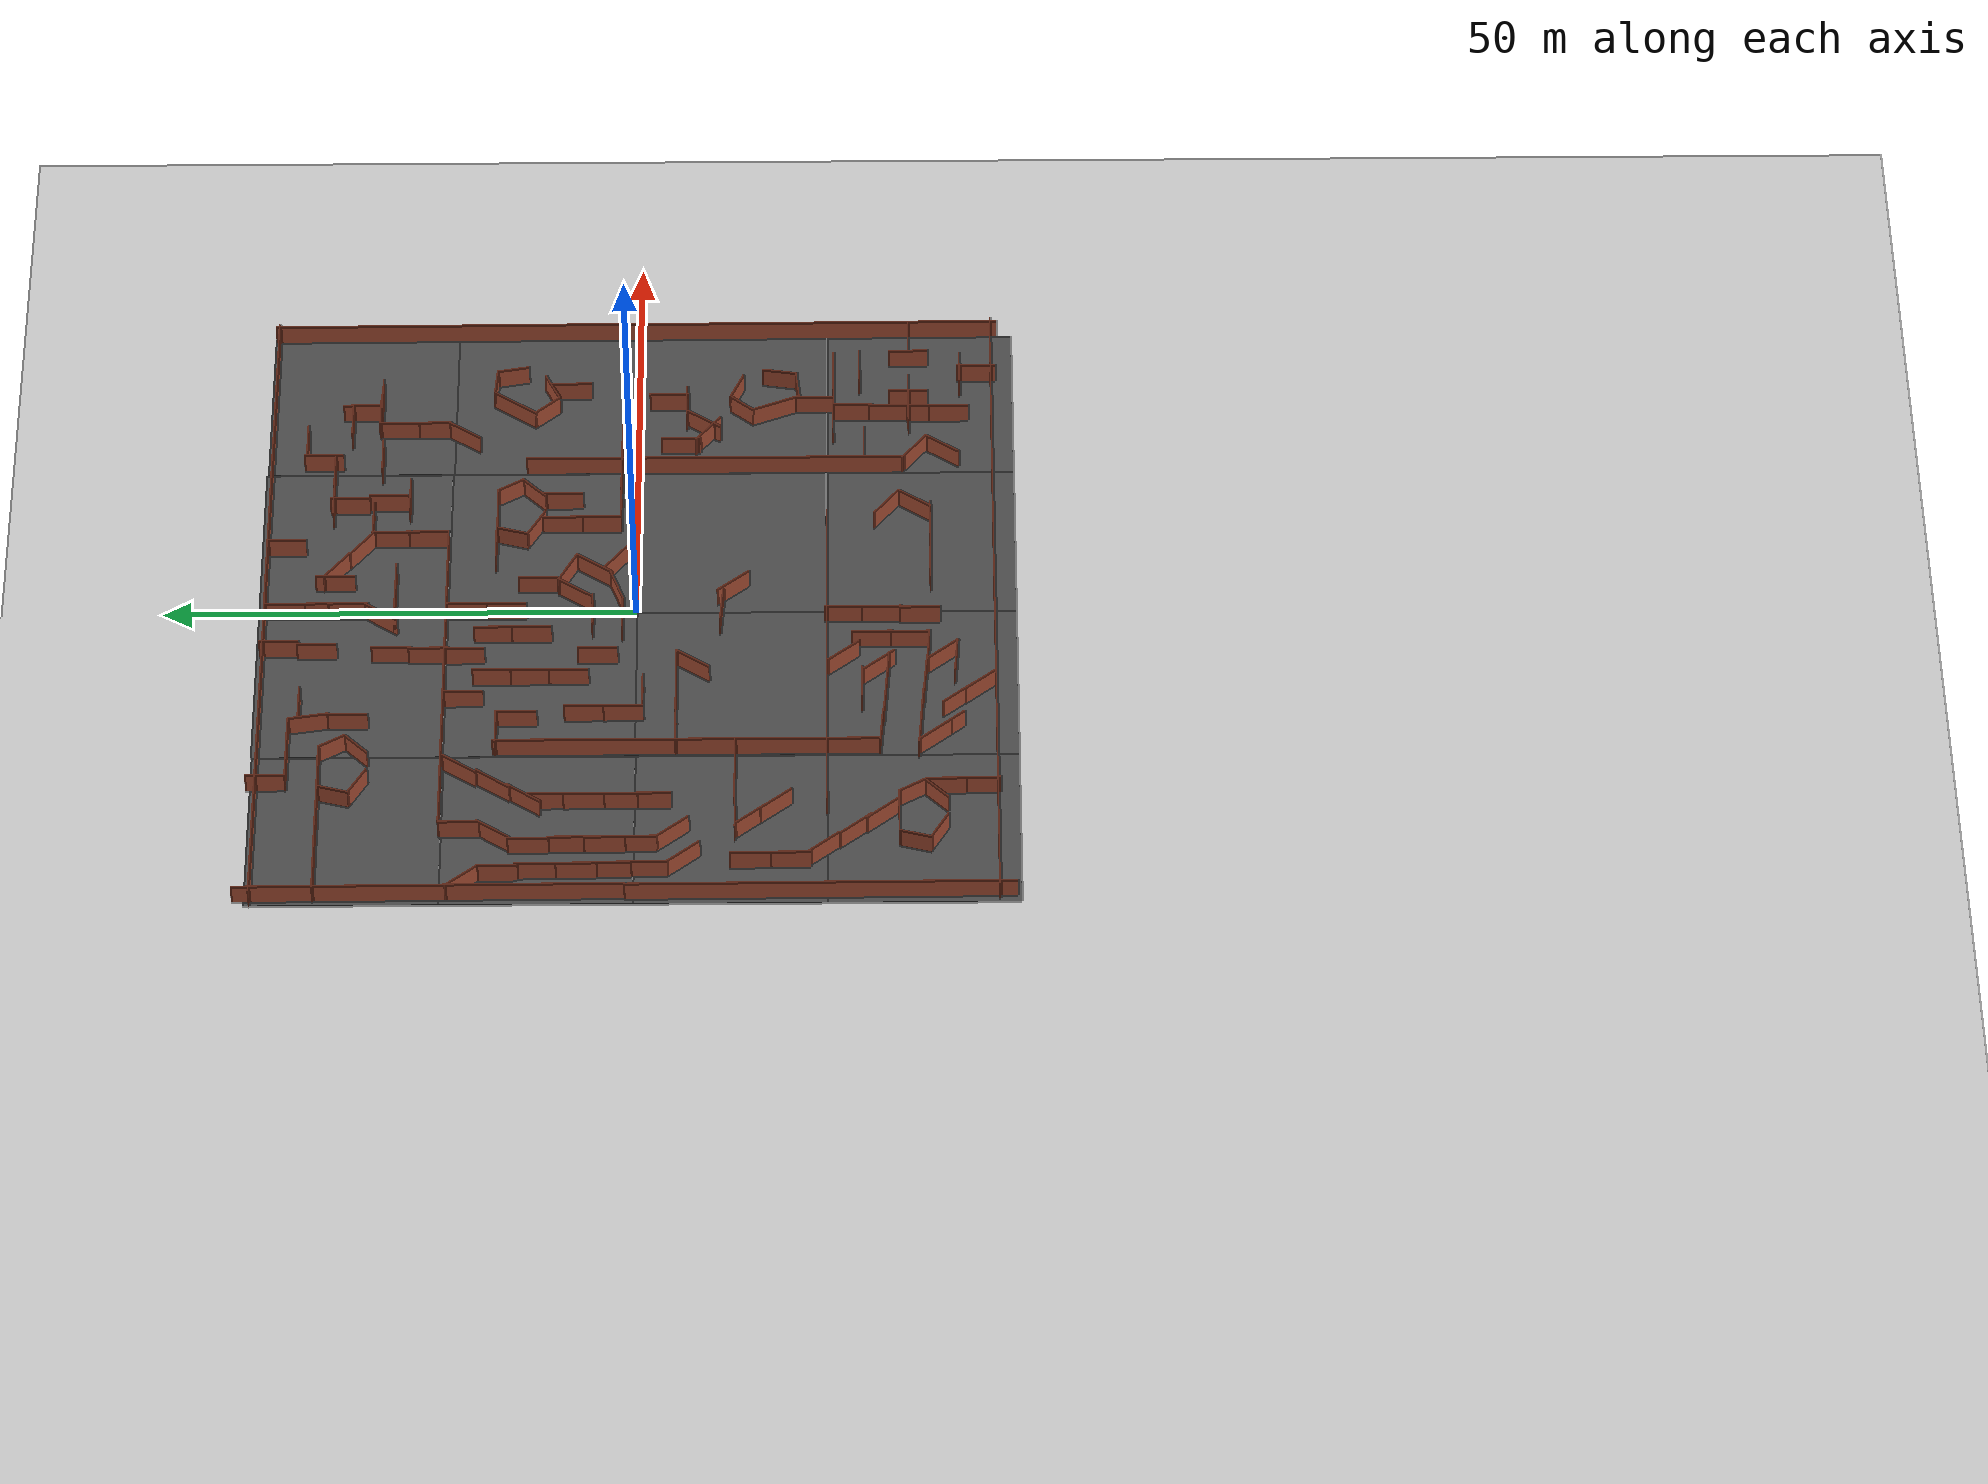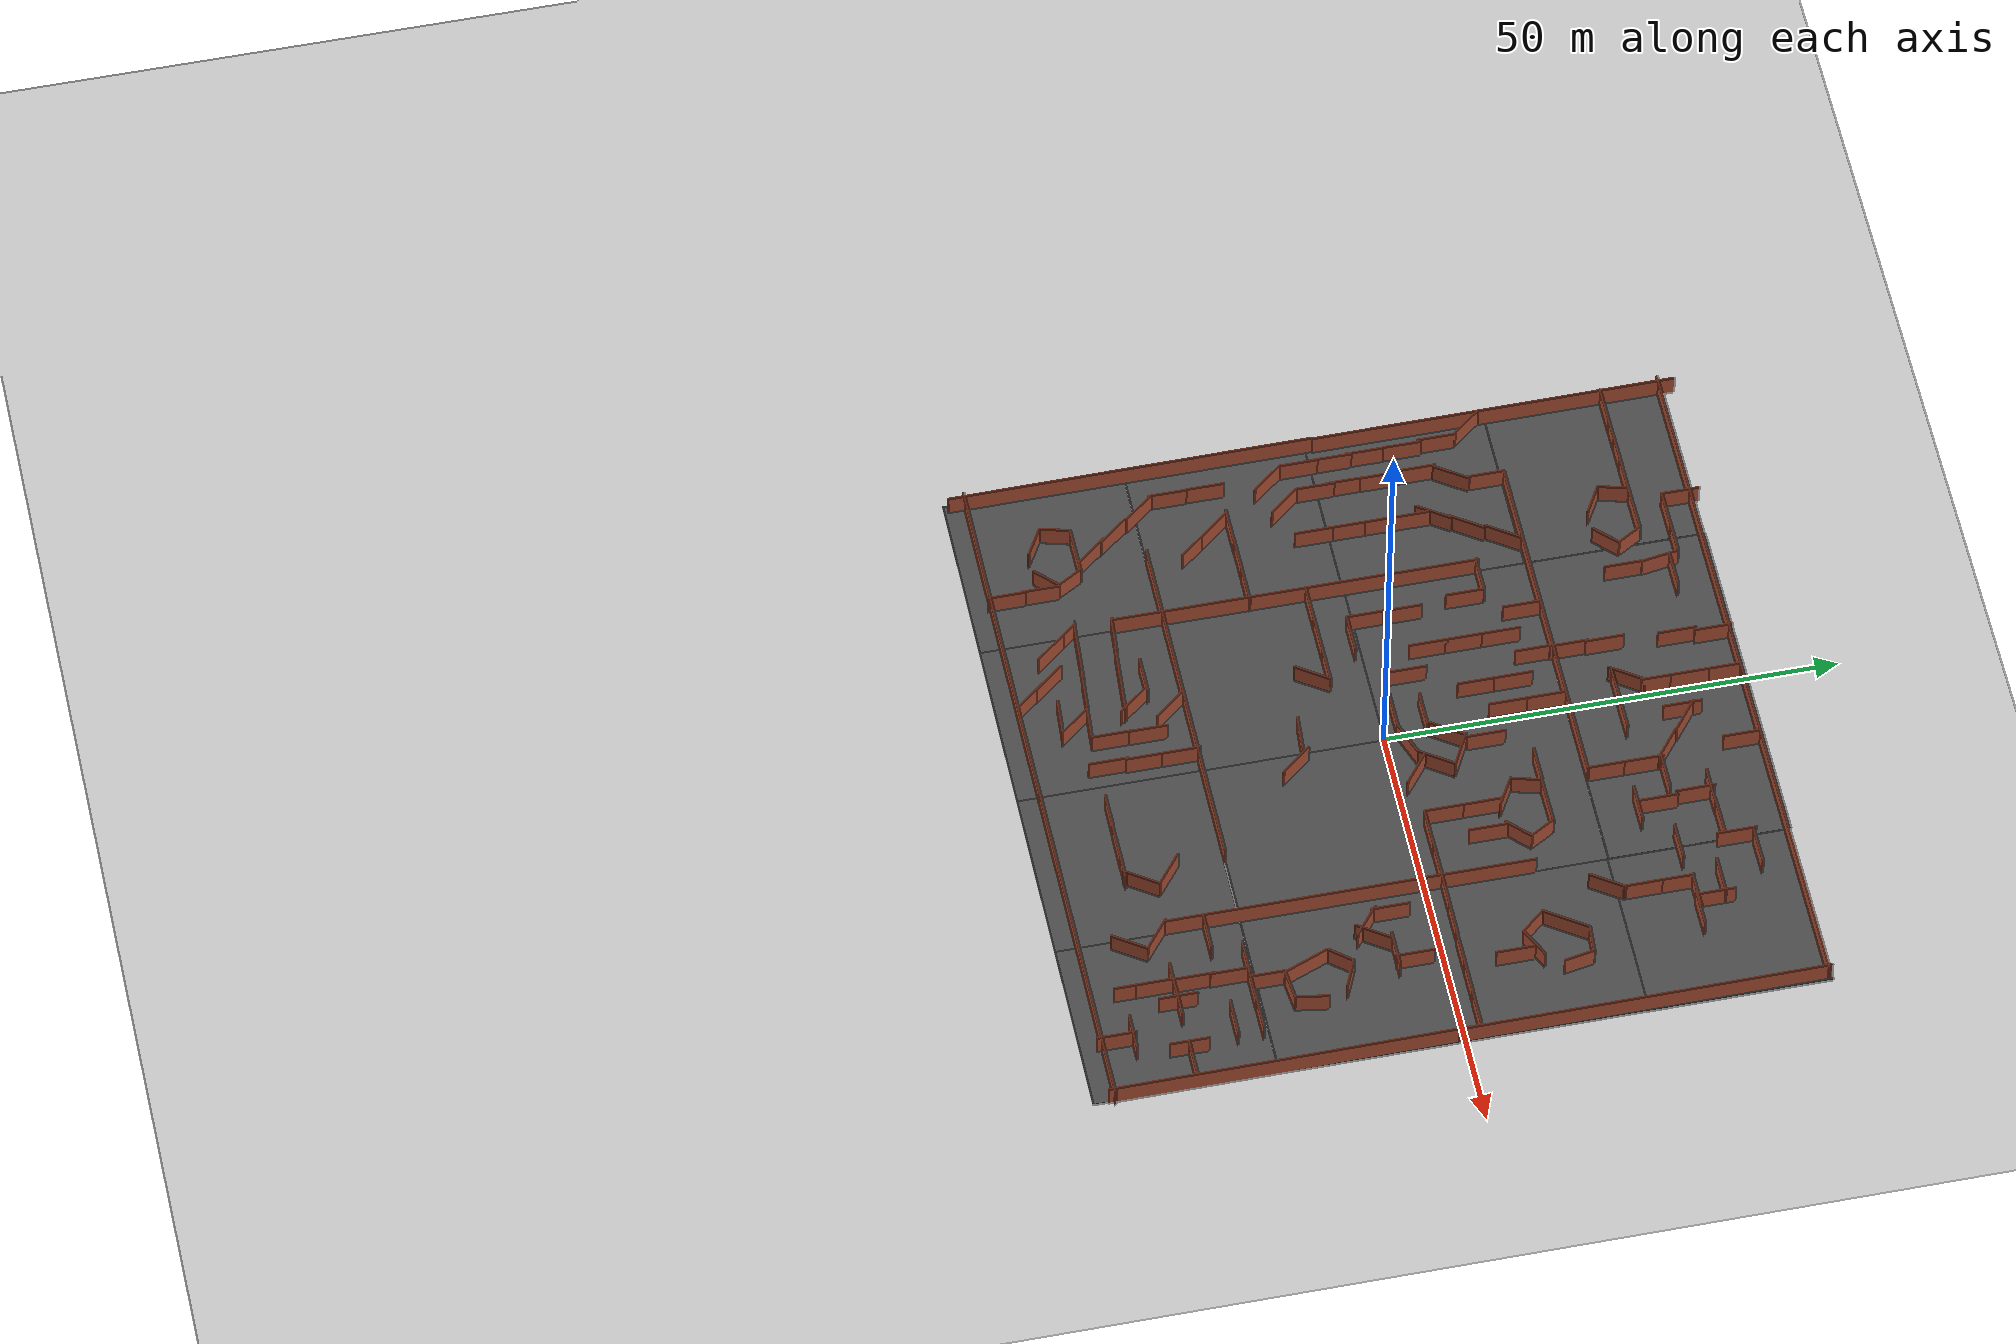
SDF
<sdf version="1.6">
 <world name="default">
  <light name="sun" type="directional">
   <pose>0 0 10 0 -0 0</pose>
   <diffuse>0.8 0.8 0.8 1</diffuse>
   <specular>0.2 0.2 0.2 1</specular>
   <attenuation>
    <range>1000</range>
    <constant>0.9</constant>
    <linear>0.01</linear>
    <quadratic>0.001</quadratic>
   </attenuation>
   <direction>-0.5 0.1 -0.9</direction>
  </light>
  <model name="ground_plane">
   <static>1</static>
   <link name="link">
    <collision name="collision">
     <geometry><plane><normal>0 0 1</normal><size>100 100</size></plane></geometry>
     <surface><friction><ode><mu>100</mu><mu2>50</mu2></ode></friction></surface>
    </collision>
    <visual name="visual">
     <cast_shadows>0</cast_shadows>
     <geometry><plane><normal>0 0 1</normal><size>100 100</size></plane></geometry>
     <material>
      <script><uri>file://media/materials/scripts/gazebo.material</uri><name>Gazebo/Grey</name></script>
     </material>
    </visual>
   </link>
  </model>
  <physics name="default_physics" default="0" type="ode">
   <max_step_size>0.001</max_step_size>
   <real_time_factor>1</real_time_factor>
   <real_time_update_rate>1000</real_time_update_rate>
  </physics>
  <scene><ambient>0.4 0.4 0.4 1</ambient><background>0.7 0.7 0.7 1</background><shadows>1</shadows></scene>
  <spherical_coordinates>
   <surface_model>EARTH_WGS84</surface_model>
   <latitude_deg>0</latitude_deg>
   <longitude_deg>0</longitude_deg>
   <elevation>0</elevation>
   <heading_deg>0</heading_deg>
  </spherical_coordinates>
  <model name="asphalt_plane">
   <static>1</static>
   <link name="link">
    <collision name="collision"><geometry><box><size>20 20 0.1</size></box></geometry></collision>
    <visual name="visual">
     <cast_shadows>0</cast_shadows>
     <geometry><box><size>20 20 0.1</size></box></geometry>
     <material>
      <script>
       <uri>model://asphalt_plane/materials/scripts</uri>
       <uri>model://asphalt_plane/materials/textures</uri>
       <name>vrc/asphalt</name>
      </script>
     </material>
    </visual>
   </link>
   <pose>10 10 0 0 -0 0</pose>
  </model>
  <model name="asphalt_plane_0">
   <static>1</static>
   <link name="link">
    <collision name="collision"><geometry><box><size>20 20 0.1</size></box></geometry></collision>
    <visual name="visual">
     <cast_shadows>0</cast_shadows>
     <geometry><box><size>20 20 0.1</size></box></geometry>
     <material>
      <script>
       <uri>model://asphalt_plane/materials/scripts</uri>
       <uri>model://asphalt_plane/materials/textures</uri>
       <name>vrc/asphalt</name>
      </script>
     </material>
    </visual>
   </link>
   <pose>-10 10 0 0 -0 0</pose>
  </model>
  <model name="asphalt_plane_1">
   <static>1</static>
   <link name="link">
    <collision name="collision"><geometry><box><size>20 20 0.1</size></box></geometry></collision>
    <visual name="visual">
     <cast_shadows>0</cast_shadows>
     <geometry><box><size>20 20 0.1</size></box></geometry>
     <material>
      <script>
       <uri>model://asphalt_plane/materials/scripts</uri>
       <uri>model://asphalt_plane/materials/textures</uri>
       <name>vrc/asphalt</name>
      </script>
     </material>
    </visual>
   </link>
   <pose>-10 -10 0 0 -0 0</pose>
  </model>
  <model name="asphalt_plane_2">
   <static>1</static>
   <link name="link">
    <collision name="collision"><geometry><box><size>20 20 0.1</size></box></geometry></collision>
    <visual name="visual">
     <cast_shadows>0</cast_shadows>
     <geometry><box><size>20 20 0.1</size></box></geometry>
     <material>
      <script>
       <uri>model://asphalt_plane/materials/scripts</uri>
       <uri>model://asphalt_plane/materials/textures</uri>
       <name>vrc/asphalt</name>
      </script>
     </material>
    </visual>
   </link>
   <pose>10 -10 0 0 -0 0</pose>
  </model>
  <model name="longwall_0_clone">
   <pose>20.0948 -8.17942 0 0 0 -1.57092</pose>
   <link name="Wall_0">
    <collision name="Wall_0_Collision">
     <geometry><box><size>40.5 0.15 2.5</size></box></geometry>
     <pose>0 0 1.25 0 -0 0</pose>
    </collision>
    <visual name="Wall_0_Visual">
     <pose>0 0 1.25 0 -0 0</pose>
     <geometry><box><size>40.5 0.15 2.5</size></box></geometry>
     <material>
      <script><uri>file://media/materials/scripts/gazebo.material</uri><name>Gazebo/Bricks</name></script>
      <ambient>1 1 1 1</ambient>
     </material>
    </visual>
    <pose>1e-06 0 0 0 -0 0</pose>
   </link>
   <static>1</static>
  </model>
  <model name="longwall_clone">
   <pose>-10.5339 20.0862 0 0 -0 0</pose>
   <link name="Wall_0">
    <collision name="Wall_0_Collision">
     <geometry><box><size>40.5 0.15 2.5</size></box></geometry>
     <pose>0 0 1.25 0 -0 0</pose>
    </collision>
    <visual name="Wall_0_Visual">
     <pose>0 0 1.25 0 -0 0</pose>
     <geometry><box><size>40.5 0.15 2.5</size></box></geometry>
     <material>
      <script><uri>file://media/materials/scripts/gazebo.material</uri><name>Gazebo/Bricks</name></script>
      <ambient>1 1 1 1</ambient>
     </material>
    </visual>
    <pose>1e-06 0 0 0 -0 0</pose>
   </link>
   <static>1</static>
  </model>
  <model name="room1">
   <pose>13.1523 12.4323 0 0 -0 0</pose>
   <link name="Wall_11">
    <collision name="Wall_11_Collision">
     <geometry><box><size>3.25 0.15 2.5</size></box></geometry>
     <pose>0 0 1.25 0 -0 0</pose>
    </collision>
    <visual name="Wall_11_Visual">
     <pose>0 0 1.25 0 -0 0</pose>
     <geometry><box><size>3.25 0.15 2.5</size></box></geometry>
     <material>
      <script><uri>file://media/materials/scripts/gazebo.material</uri><name>Gazebo/Bricks</name></script>
      <ambient>1 1 1 1</ambient>
     </material>
    </visual>
    <pose>3.12132 1.19483 0 0 0 -1.0472</pose>
   </link>
   <link name="Wall_12">
    <collision name="Wall_12_Collision">
     <geometry><box><size>3.5 0.15 2.5</size></box></geometry>
     <pose>0 0 1.25 0 -0 0</pose>
    </collision>
    <visual name="Wall_12_Visual">
     <pose>0 0 1.25 0 -0 0</pose>
     <geometry><box><size>3.5 0.15 2.5</size></box></geometry>
     <material>
      <script><uri>file://media/materials/scripts/gazebo.material</uri><name>Gazebo/Bricks</name></script>
      <ambient>1 1 1 1</ambient>
     </material>
    </visual>
    <pose>2.71192 -1.33192 0 0 0 -2.35619</pose>
   </link>
   <link name="Wall_7">
    <collision name="Wall_7_Collision">
     <geometry><box><size>5.52935 0.15 2.5</size></box></geometry>
     <pose>0 0 1.25 0 -0 0</pose>
    </collision>
    <visual name="Wall_7_Visual">
     <pose>0 0 1.25 0 -0 0</pose>
     <geometry><box><size>5.52935 0.15 2.5</size></box></geometry>
     <material>
      <script><uri>file://media/materials/scripts/gazebo.material</uri><name>Gazebo/Bricks</name></script>
      <ambient>1 1 1 1</ambient>
     </material>
    </visual>
    <pose>-0.343285 2.51793 0 0 0 -3.13444</pose>
   </link>
   <link name="Wall_8">
    <collision name="Wall_8_Collision">
     <geometry><box><size>3.5 0.15 2.5</size></box></geometry>
     <pose>0 0 1.25 0 -0 0</pose>
    </collision>
    <visual name="Wall_8_Visual">
     <pose>0 0 1.25 0 -0 0</pose>
     <geometry><box><size>3.5 0.15 2.5</size></box></geometry>
     <material>
      <script><uri>file://media/materials/scripts/gazebo.material</uri><name>Gazebo/Bricks</name></script>
      <ambient>1 1 1 1</ambient>
     </material>
    </visual>
    <pose>-3.46641 0.880761 0 0 0 -1.8326</pose>
   </link>
   <link name="Wall_9">
    <collision name="Wall_9_Collision">
     <geometry><box><size>3.75 0.15 2.5</size></box></geometry>
     <pose>0 0 1.25 0 -0 0</pose>
    </collision>
    <visual name="Wall_9_Visual">
     <pose>0 0 1.25 0 -0 0</pose>
     <geometry><box><size>3.75 0.15 2.5</size></box></geometry>
     <material>
      <script><uri>file://media/materials/scripts/gazebo.material</uri><name>Gazebo/Bricks</name></script>
      <ambient>1 1 1 1</ambient>
     </material>
    </visual>
    <pose>-2.34109 -1.63716 0 0 0 -0.523599</pose>
   </link>
   <static>1</static>
  </model>
  <model name="worlds_1">
   <pose>3 10.4406 0 0 -0 0</pose>
   <link name="Wall_0">
    <collision name="Wall_0_Collision">
     <geometry><box><size>4.25 0.15 2.5</size></box></geometry>
     <pose>0 0 1.25 0 -0 0</pose>
    </collision>
    <visual name="Wall_0_Visual">
     <pose>0 0 1.25 0 -0 0</pose>
     <geometry><box><size>4.25 0.15 2.5</size></box></geometry>
     <material>
      <script><uri>file://media/materials/scripts/gazebo.material</uri><name>Gazebo/Bricks</name></script>
      <ambient>1 1 1 1</ambient>
     </material>
    </visual>
    <pose>0 -0 0 0 -0 1.5708</pose>
   </link>
   <static>1</static>
  </model>
  <model name="worlds_2">
   <pose>4.42901 7.33195 0 0 -0 1.08023</pose>
   <link name="Wall_0">
    <collision name="Wall_0_Collision">
     <geometry><box><size>4.25 0.15 2.5</size></box></geometry>
     <pose>0 0 1.25 0 -0 0</pose>
    </collision>
    <visual name="Wall_0_Visual">
     <pose>0 0 1.25 0 -0 0</pose>
     <geometry><box><size>4.25 0.15 2.5</size></box></geometry>
     <material>
      <script><uri>file://media/materials/scripts/gazebo.material</uri><name>Gazebo/Bricks</name></script>
      <ambient>1 1 1 1</ambient>
     </material>
    </visual>
    <pose>0 -0 0 0 -0 1.5708</pose>
   </link>
   <static>1</static>
  </model>
  <model name="worlds_0_clone">
   <pose>-1 -9 0 0 -0 1.49697</pose>
   <link name="Wall_0">
    <collision name="Wall_0_Collision">
     <geometry><box><size>4.25 0.15 2.5</size></box></geometry>
     <pose>0 0 1.25 0 -0 0</pose>
    </collision>
    <visual name="Wall_0_Visual">
     <pose>0 0 1.25 0 -0 0</pose>
     <geometry><box><size>4.25 0.15 2.5</size></box></geometry>
     <material>
      <script><uri>file://media/materials/scripts/gazebo.material</uri><name>Gazebo/Bricks</name></script>
      <ambient>1 1 1 1</ambient>
     </material>
    </visual>
    <pose>0 -0 0 0 -0 1.5708</pose>
   </link>
   <static>1</static>
  </model>
  <model name="worlds_2_clone">
   <pose>2.34689 -10.1873 0 0 -0 0.67691</pose>
   <link name="Wall_0">
    <collision name="Wall_0_Collision">
     <geometry><box><size>4.25 0.15 2.5</size></box></geometry>
     <pose>0 0 1.25 0 -0 0</pose>
    </collision>
    <visual name="Wall_0_Visual">
     <pose>0 0 1.25 0 -0 0</pose>
     <geometry><box><size>4.25 0.15 2.5</size></box></geometry>
     <material>
      <script><uri>file://media/materials/scripts/gazebo.material</uri><name>Gazebo/Bricks</name></script>
      <ambient>1 1 1 1</ambient>
     </material>
    </visual>
    <pose>0 -0 0 0 -0 1.5708</pose>
   </link>
   <static>1</static>
  </model>
  <model name="worlds_1_clone">
   <pose>11.6021 8.07399 0 0 -0 0</pose>
   <link name="Wall_0">
    <collision name="Wall_0_Collision">
     <geometry><box><size>4.25 0.15 2.5</size></box></geometry>
     <pose>0 0 1.25 0 -0 0</pose>
    </collision>
    <visual name="Wall_0_Visual">
     <pose>0 0 1.25 0 -0 0</pose>
     <geometry><box><size>4.25 0.15 2.5</size></box></geometry>
     <material>
      <script><uri>file://media/materials/scripts/gazebo.material</uri><name>Gazebo/Bricks</name></script>
      <ambient>1 1 1 1</ambient>
     </material>
    </visual>
    <pose>0 -0 0 0 -0 1.5708</pose>
   </link>
   <static>1</static>
  </model>
  <model name="worlds_1_clone_0">
   <pose>11.6134 3.89135 0 0 -0 0</pose>
   <link name="Wall_0">
    <collision name="Wall_0_Collision">
     <geometry><box><size>4.25 0.15 2.5</size></box></geometry>
     <pose>0 0 1.25 0 -0 0</pose>
    </collision>
    <visual name="Wall_0_Visual">
     <pose>0 0 1.25 0 -0 0</pose>
     <geometry><box><size>4.25 0.15 2.5</size></box></geometry>
     <material>
      <script><uri>file://media/materials/scripts/gazebo.material</uri><name>Gazebo/Bricks</name></script>
      <ambient>1 1 1 1</ambient>
     </material>
    </visual>
    <pose>0 -0 0 0 -0 1.5708</pose>
   </link>
   <static>1</static>
  </model>
  <model name="worlds_1_clone_0_clone">
   <pose>13.736 1.79456 0 0 0 -1.57092</pose>
   <link name="Wall_0">
    <collision name="Wall_0_Collision">
     <geometry><box><size>4.25 0.15 2.5</size></box></geometry>
     <pose>0 0 1.25 0 -0 0</pose>
    </collision>
    <visual name="Wall_0_Visual">
     <pose>0 0 1.25 0 -0 0</pose>
     <geometry><box><size>4.25 0.15 2.5</size></box></geometry>
     <material>
      <script><uri>file://media/materials/scripts/gazebo.material</uri><name>Gazebo/Bricks</name></script>
      <ambient>1 1 1 1</ambient>
     </material>
    </visual>
    <pose>0 -0 0 0 -0 1.5708</pose>
   </link>
   <static>1</static>
  </model>
  <model name="worlds_1_clone_0_clone_clone">
   <pose>17.9203 1.82357 0 0 0 -1.57092</pose>
   <link name="Wall_0">
    <collision name="Wall_0_Collision">
     <geometry><box><size>4.25 0.15 2.5</size></box></geometry>
     <pose>0 0 1.25 0 -0 0</pose>
    </collision>
    <visual name="Wall_0_Visual">
     <pose>0 0 1.25 0 -0 0</pose>
     <geometry><box><size>4.25 0.15 2.5</size></box></geometry>
     <material>
      <script><uri>file://media/materials/scripts/gazebo.material</uri><name>Gazebo/Bricks</name></script>
      <ambient>1 1 1 1</ambient>
     </material>
    </visual>
    <pose>0 -0 0 0 -0 1.5708</pose>
   </link>
   <static>1</static>
  </model>
  <model name="worlds_1_clone_0_clone_clone_0">
   <pose>8 15 0 0 0 -1.57092</pose>
   <link name="Wall_0">
    <collision name="Wall_0_Collision">
     <geometry><box><size>4.25 0.15 2.5</size></box></geometry>
     <pose>0 0 1.25 0 -0 0</pose>
    </collision>
    <visual name="Wall_0_Visual">
     <pose>0 0 1.25 0 -0 0</pose>
     <geometry><box><size>4.25 0.15 2.5</size></box></geometry>
     <material>
      <script><uri>file://media/materials/scripts/gazebo.material</uri><name>Gazebo/Bricks</name></script>
      <ambient>1 1 1 1</ambient>
     </material>
    </visual>
    <pose>0 -0 0 0 -0 1.5708</pose>
   </link>
   <static>1</static>
  </model>
  <model name="worlds_1_clone_0_clone_clone_0_clone">
   <pose>-17.8162 14.4688 0 0 0 -1.57092</pose>
   <link name="Wall_0">
    <collision name="Wall_0_Collision">
     <geometry><box><size>4.25 0.15 2.5</size></box></geometry>
     <pose>0 0 1.25 0 -0 0</pose>
    </collision>
    <visual name="Wall_0_Visual">
     <pose>0 0 1.25 0 -0 0</pose>
     <geometry><box><size>4.25 0.15 2.5</size></box></geometry>
     <material>
      <script><uri>file://media/materials/scripts/gazebo.material</uri><name>Gazebo/Bricks</name></script>
      <ambient>1 1 1 1</ambient>
     </material>
    </visual>
    <pose>0 -0 0 0 -0 1.5708</pose>
   </link>
   <static>1</static>
  </model>
  <model name="worlds_1_clone_1">
   <pose>-13 18 0 0 -0 0</pose>
   <link name="Wall_0">
    <collision name="Wall_0_Collision">
     <geometry><box><size>4.25 0.15 2.5</size></box></geometry>
     <pose>0 0 1.25 0 -0 0</pose>
    </collision>
    <visual name="Wall_0_Visual">
     <pose>0 0 1.25 0 -0 0</pose>
     <geometry><box><size>4.25 0.15 2.5</size></box></geometry>
     <material>
      <script><uri>file://media/materials/scripts/gazebo.material</uri><name>Gazebo/Bricks</name></script>
      <ambient>1 1 1 1</ambient>
     </material>
    </visual>
    <pose>0 -0 0 0 -0 1.5708</pose>
   </link>
   <static>1</static>
  </model>
  <model name="worlds_1_clone_1_clone">
   <pose>-15.7734 12.3225 0 0 -0 0</pose>
   <link name="Wall_0">
    <collision name="Wall_0_Collision">
     <geometry><box><size>4.25 0.15 2.5</size></box></geometry>
     <pose>0 0 1.25 0 -0 0</pose>
    </collision>
    <visual name="Wall_0_Visual">
     <pose>0 0 1.25 0 -0 0</pose>
     <geometry><box><size>4.25 0.15 2.5</size></box></geometry>
     <material>
      <script><uri>file://media/materials/scripts/gazebo.material</uri><name>Gazebo/Bricks</name></script>
      <ambient>1 1 1 1</ambient>
     </material>
    </visual>
    <pose>0 -0 0 0 -0 1.5708</pose>
   </link>
   <static>1</static>
  </model>
  <model name="worlds_1_clone_1_clone_clone">
   <pose>-15.0638 5.287 0 0 -0 0</pose>
   <link name="Wall_0">
    <collision name="Wall_0_Collision">
     <geometry><box><size>4.25 0.15 2.5</size></box></geometry>
     <pose>0 0 1.25 0 -0 0</pose>
    </collision>
    <visual name="Wall_0_Visual">
     <pose>0 0 1.25 0 -0 0</pose>
     <geometry><box><size>4.25 0.15 2.5</size></box></geometry>
     <material>
      <script><uri>file://media/materials/scripts/gazebo.material</uri><name>Gazebo/Bricks</name></script>
      <ambient>1 1 1 1</ambient>
     </material>
    </visual>
    <pose>0 -0 0 0 -0 1.5708</pose>
   </link>
   <static>1</static>
  </model>
  <model name="worlds_1_clone_1_clone_clone_0">
   <pose>-15.0769 1.18275 0 0 -0 0</pose>
   <link name="Wall_0">
    <collision name="Wall_0_Collision">
     <geometry><box><size>4.25 0.15 2.5</size></box></geometry>
     <pose>0 0 1.25 0 -0 0</pose>
    </collision>
    <visual name="Wall_0_Visual">
     <pose>0 0 1.25 0 -0 0</pose>
     <geometry><box><size>4.25 0.15 2.5</size></box></geometry>
     <material>
      <script><uri>file://media/materials/scripts/gazebo.material</uri><name>Gazebo/Bricks</name></script>
      <ambient>1 1 1 1</ambient>
     </material>
    </visual>
    <pose>0 -0 0 0 -0 1.5708</pose>
   </link>
   <static>1</static>
  </model>
  <model name="worlds_1_clone_0_clone_clone_0_clone_clone">
   <pose>-17.8054 -4.32089 0 0 0 -1.57092</pose>
   <link name="Wall_0">
    <collision name="Wall_0_Collision">
     <geometry><box><size>4.25 0.15 2.5</size></box></geometry>
     <pose>0 0 1.25 0 -0 0</pose>
    </collision>
    <visual name="Wall_0_Visual">
     <pose>0 0 1.25 0 -0 0</pose>
     <geometry><box><size>4.25 0.15 2.5</size></box></geometry>
     <material>
      <script><uri>file://media/materials/scripts/gazebo.material</uri><name>Gazebo/Bricks</name></script>
      <ambient>1 1 1 1</ambient>
     </material>
    </visual>
    <pose>0 -0 0 0 -0 1.5708</pose>
   </link>
   <static>1</static>
  </model>
  <model name="worlds_1_clone_0_clone_clone_0_clone_clone_0">
   <pose>-13.6699 -4.29855 0 0 0 -1.57092</pose>
   <link name="Wall_0">
    <collision name="Wall_0_Collision">
     <geometry><box><size>4.25 0.15 2.5</size></box></geometry>
     <pose>0 0 1.25 0 -0 0</pose>
    </collision>
    <visual name="Wall_0_Visual">
     <pose>0 0 1.25 0 -0 0</pose>
     <geometry><box><size>4.25 0.15 2.5</size></box></geometry>
     <material>
      <script><uri>file://media/materials/scripts/gazebo.material</uri><name>Gazebo/Bricks</name></script>
      <ambient>1 1 1 1</ambient>
     </material>
    </visual>
    <pose>0 -0 0 0 -0 1.5708</pose>
   </link>
   <static>1</static>
  </model>
  <model name="worlds_1_clone_0_clone_clone_0_clone_clone_1">
   <pose>-9.47339 -4.28892 0 0 0 -1.57092</pose>
   <link name="Wall_0">
    <collision name="Wall_0_Collision">
     <geometry><box><size>4.25 0.15 2.5</size></box></geometry>
     <pose>0 0 1.25 0 -0 0</pose>
    </collision>
    <visual name="Wall_0_Visual">
     <pose>0 0 1.25 0 -0 0</pose>
     <geometry><box><size>4.25 0.15 2.5</size></box></geometry>
     <material>
      <script><uri>file://media/materials/scripts/gazebo.material</uri><name>Gazebo/Bricks</name></script>
      <ambient>1 1 1 1</ambient>
     </material>
    </visual>
    <pose>0 -0 0 0 -0 1.5708</pose>
   </link>
   <static>1</static>
  </model>
  <model name="worlds_1_clone_1_clone_0">
   <pose>-0.708445 17.9147 0 0 -0 0</pose>
   <link name="Wall_0">
    <collision name="Wall_0_Collision">
     <geometry><box><size>4.25 0.15 2.5</size></box></geometry>
     <pose>0 0 1.25 0 -0 0</pose>
    </collision>
    <visual name="Wall_0_Visual">
     <pose>0 0 1.25 0 -0 0</pose>
     <geometry><box><size>4.25 0.15 2.5</size></box></geometry>
     <material>
      <script><uri>file://media/materials/scripts/gazebo.material</uri><name>Gazebo/Bricks</name></script>
      <ambient>1 1 1 1</ambient>
     </material>
    </visual>
    <pose>0 -0 0 0 -0 1.5708</pose>
   </link>
   <static>1</static>
  </model>
  <model name="worlds_1_clone_1_clone_1">
   <pose>-0.716318 13.714 0 0 -0 0</pose>
   <link name="Wall_0">
    <collision name="Wall_0_Collision">
     <geometry><box><size>4.25 0.15 2.5</size></box></geometry>
     <pose>0 0 1.25 0 -0 0</pose>
    </collision>
    <visual name="Wall_0_Visual">
     <pose>0 0 1.25 0 -0 0</pose>
     <geometry><box><size>4.25 0.15 2.5</size></box></geometry>
     <material>
      <script><uri>file://media/materials/scripts/gazebo.material</uri><name>Gazebo/Bricks</name></script>
      <ambient>1 1 1 1</ambient>
     </material>
    </visual>
    <pose>0 -0 0 0 -0 1.5708</pose>
   </link>
   <static>1</static>
  </model>
  <model name="worlds_1_clone_1_clone_2">
   <pose>-7 18 0 0 -0 0</pose>
   <link name="Wall_0">
    <collision name="Wall_0_Collision">
     <geometry><box><size>4.25 0.15 2.5</size></box></geometry>
     <pose>0 0 1.25 0 -0 0</pose>
    </collision>
    <visual name="Wall_0_Visual">
     <pose>0 0 1.25 0 -0 0</pose>
     <geometry><box><size>4.25 0.15 2.5</size></box></geometry>
     <material>
      <script><uri>file://media/materials/scripts/gazebo.material</uri><name>Gazebo/Bricks</name></script>
      <ambient>1 1 1 1</ambient>
     </material>
    </visual>
    <pose>0 -0 0 0 -0 1.5708</pose>
   </link>
   <static>1</static>
  </model>
  <model name="worlds_1_clone_1_clone_3">
   <pose>-10 15 0 0 -0 0</pose>
   <link name="Wall_0">
    <collision name="Wall_0_Collision">
     <geometry><box><size>4.25 0.15 2.5</size></box></geometry>
     <pose>0 0 1.25 0 -0 0</pose>
    </collision>
    <visual name="Wall_0_Visual">
     <pose>0 0 1.25 0 -0 0</pose>
     <geometry><box><size>4.25 0.15 2.5</size></box></geometry>
     <material>
      <script><uri>file://media/materials/scripts/gazebo.material</uri><name>Gazebo/Bricks</name></script>
      <ambient>1 1 1 1</ambient>
     </material>
    </visual>
    <pose>0 -0 0 0 -0 1.5708</pose>
   </link>
   <static>1</static>
  </model>
  <model name="worlds_1_clone_1_clone_4">
   <pose>-10 11 0 0 -0 0</pose>
   <link name="Wall_0">
    <collision name="Wall_0_Collision">
     <geometry><box><size>4.25 0.15 2.5</size></box></geometry>
     <pose>0 0 1.25 0 -0 0</pose>
    </collision>
    <visual name="Wall_0_Visual">
     <pose>0 0 1.25 0 -0 0</pose>
     <geometry><box><size>4.25 0.15 2.5</size></box></geometry>
     <material>
      <script><uri>file://media/materials/scripts/gazebo.material</uri><name>Gazebo/Bricks</name></script>
      <ambient>1 1 1 1</ambient>
     </material>
    </visual>
    <pose>0 -0 0 0 -0 1.5708</pose>
   </link>
   <static>1</static>
  </model>
  <model name="worlds_1_clone_1_clone_5">
   <pose>-4 15 0 0 -0 0</pose>
   <link name="Wall_0">
    <collision name="Wall_0_Collision">
     <geometry><box><size>4.25 0.15 2.5</size></box></geometry>
     <pose>0 0 1.25 0 -0 0</pose>
    </collision>
    <visual name="Wall_0_Visual">
     <pose>0 0 1.25 0 -0 0</pose>
     <geometry><box><size>4.25 0.15 2.5</size></box></geometry>
     <material>
      <script><uri>file://media/materials/scripts/gazebo.material</uri><name>Gazebo/Bricks</name></script>
      <ambient>1 1 1 1</ambient>
     </material>
    </visual>
    <pose>0 -0 0 0 -0 1.5708</pose>
   </link>
   <static>1</static>
  </model>
  <model name="worlds_1_clone_1_clone_6">
   <pose>-4 11 0 0 -0 0</pose>
   <link name="Wall_0">
    <collision name="Wall_0_Collision">
     <geometry><box><size>4.25 0.15 2.5</size></box></geometry>
     <pose>0 0 1.25 0 -0 0</pose>
    </collision>
    <visual name="Wall_0_Visual">
     <pose>0 0 1.25 0 -0 0</pose>
     <geometry><box><size>4.25 0.15 2.5</size></box></geometry>
     <material>
      <script><uri>file://media/materials/scripts/gazebo.material</uri><name>Gazebo/Bricks</name></script>
      <ambient>1 1 1 1</ambient>
     </material>
    </visual>
    <pose>0 -0 0 0 -0 1.5708</pose>
   </link>
   <static>1</static>
  </model>
  <model name="worlds_1_clone_1_clone_7">
   <pose>-10 7 0 0 -0 0</pose>
   <link name="Wall_0">
    <collision name="Wall_0_Collision">
     <geometry><box><size>4.25 0.15 2.5</size></box></geometry>
     <pose>0 0 1.25 0 -0 0</pose>
    </collision>
    <visual name="Wall_0_Visual">
     <pose>0 0 1.25 0 -0 0</pose>
     <geometry><box><size>4.25 0.15 2.5</size></box></geometry>
     <material>
      <script><uri>file://media/materials/scripts/gazebo.material</uri><name>Gazebo/Bricks</name></script>
      <ambient>1 1 1 1</ambient>
     </material>
    </visual>
    <pose>0 -0 0 0 -0 1.5708</pose>
   </link>
   <static>1</static>
  </model>
  <model name="worlds_1_clone_0_clone_clone_0_clone_clone_0_clone">
   <pose>-12.8938 -0.809745 0 0 0 -1.57092</pose>
   <link name="Wall_0">
    <collision name="Wall_0_Collision">
     <geometry><box><size>4.25 0.15 2.5</size></box></geometry>
     <pose>0 0 1.25 0 -0 0</pose>
    </collision>
    <visual name="Wall_0_Visual">
     <pose>0 0 1.25 0 -0 0</pose>
     <geometry><box><size>4.25 0.15 2.5</size></box></geometry>
     <material>
      <script><uri>file://media/materials/scripts/gazebo.material</uri><name>Gazebo/Bricks</name></script>
      <ambient>1 1 1 1</ambient>
     </material>
    </visual>
    <pose>0 -0 0 0 -0 1.5708</pose>
   </link>
   <static>1</static>
  </model>
  <model name="worlds_1_clone_1_clone_7_clone">
   <pose>-7 4 0 0 -0 0</pose>
   <link name="Wall_0">
    <collision name="Wall_0_Collision">
     <geometry><box><size>4.25 0.15 2.5</size></box></geometry>
     <pose>0 0 1.25 0 -0 0</pose>
    </collision>
    <visual name="Wall_0_Visual">
     <pose>0 0 1.25 0 -0 0</pose>
     <geometry><box><size>4.25 0.15 2.5</size></box></geometry>
     <material>
      <script><uri>file://media/materials/scripts/gazebo.material</uri><name>Gazebo/Bricks</name></script>
      <ambient>1 1 1 1</ambient>
     </material>
    </visual>
    <pose>0 -0 0 0 -0 1.5708</pose>
   </link>
   <static>1</static>
  </model>
  <model name="worlds_1_clone_1_clone_7_clone_clone">
   <pose>1.48825 6.4581 0 0 0 -0.589381</pose>
   <link name="Wall_0">
    <collision name="Wall_0_Collision">
     <geometry><box><size>4.25 0.15 2.5</size></box></geometry>
     <pose>0 0 1.25 0 -0 0</pose>
    </collision>
    <visual name="Wall_0_Visual">
     <pose>0 0 1.25 0 -0 0</pose>
     <geometry><box><size>4.25 0.15 2.5</size></box></geometry>
     <material>
      <script><uri>file://media/materials/scripts/gazebo.material</uri><name>Gazebo/Bricks</name></script>
      <ambient>1 1 1 1</ambient>
     </material>
    </visual>
    <pose>0 -0 0 0 -0 1.5708</pose>
   </link>
   <static>1</static>
  </model>
  <model name="worlds_1_clone_1_clone_7_clone_clone_clone">
   <pose>5 4.58681 0 0 0 -0.589381</pose>
   <link name="Wall_0">
    <collision name="Wall_0_Collision">
     <geometry><box><size>4.25 0.15 2.5</size></box></geometry>
     <pose>0 0 1.25 0 -0 0</pose>
    </collision>
    <visual name="Wall_0_Visual">
     <pose>0 0 1.25 0 -0 0</pose>
     <geometry><box><size>4.25 0.15 2.5</size></box></geometry>
     <material>
      <script><uri>file://media/materials/scripts/gazebo.material</uri><name>Gazebo/Bricks</name></script>
      <ambient>1 1 1 1</ambient>
     </material>
    </visual>
    <pose>0 -0 0 0 -0 1.5708</pose>
   </link>
   <static>1</static>
  </model>
  <model name="worlds_1_clone_0_clone_clone_0_clone_clone_0_clone_clone">
   <pose>-1.54431 4.60476 0 0 0 -1.57092</pose>
   <link name="Wall_0">
    <collision name="Wall_0_Collision">
     <geometry><box><size>4.25 0.15 2.5</size></box></geometry>
     <pose>0 0 1.25 0 -0 0</pose>
    </collision>
    <visual name="Wall_0_Visual">
     <pose>0 0 1.25 0 -0 0</pose>
     <geometry><box><size>4.25 0.15 2.5</size></box></geometry>
     <material>
      <script><uri>file://media/materials/scripts/gazebo.material</uri><name>Gazebo/Bricks</name></script>
      <ambient>1 1 1 1</ambient>
     </material>
    </visual>
    <pose>0 -0 0 0 -0 1.5708</pose>
   </link>
   <static>1</static>
  </model>
  <model name="worlds_1_clone_0_clone_clone_0_clone_clone_0_clone_clone_0">
   <pose>1.87166 2.0906 0 0 0 -1.22347</pose>
   <link name="Wall_0">
    <collision name="Wall_0_Collision">
     <geometry><box><size>4.25 0.15 2.5</size></box></geometry>
     <pose>0 0 1.25 0 -0 0</pose>
    </collision>
    <visual name="Wall_0_Visual">
     <pose>0 0 1.25 0 -0 0</pose>
     <geometry><box><size>4.25 0.15 2.5</size></box></geometry>
     <material>
      <script><uri>file://media/materials/scripts/gazebo.material</uri><name>Gazebo/Bricks</name></script>
      <ambient>1 1 1 1</ambient>
     </material>
    </visual>
    <pose>0 -0 0 0 -0 1.5708</pose>
   </link>
   <static>1</static>
  </model>
  <model name="worlds_1_clone_0_clone_clone_0_clone_clone_0_clone_clone_clone">
   <pose>-2 1.45154 0 0 0 -1.57092</pose>
   <link name="Wall_0">
    <collision name="Wall_0_Collision">
     <geometry><box><size>4.25 0.15 2.5</size></box></geometry>
     <pose>0 0 1.25 0 -0 0</pose>
    </collision>
    <visual name="Wall_0_Visual">
     <pose>0 0 1.25 0 -0 0</pose>
     <geometry><box><size>4.25 0.15 2.5</size></box></geometry>
     <material>
      <script><uri>file://media/materials/scripts/gazebo.material</uri><name>Gazebo/Bricks</name></script>
      <ambient>1 1 1 1</ambient>
     </material>
    </visual>
    <pose>0 -0 0 0 -0 1.5708</pose>
   </link>
   <static>1</static>
  </model>
  <model name="worlds_1_clone_1_clone_7_clone_clone_0">
   <pose>6.00131 2.13117 0 0 -0 0.90029</pose>
   <link name="Wall_0">
    <collision name="Wall_0_Collision">
     <geometry><box><size>4.25 0.15 2.5</size></box></geometry>
     <pose>0 0 1.25 0 -0 0</pose>
    </collision>
    <visual name="Wall_0_Visual">
     <pose>0 0 1.25 0 -0 0</pose>
     <geometry><box><size>4.25 0.15 2.5</size></box></geometry>
     <material>
      <script><uri>file://media/materials/scripts/gazebo.material</uri><name>Gazebo/Bricks</name></script>
      <ambient>1 1 1 1</ambient>
     </material>
    </visual>
    <pose>0 -0 0 0 -0 1.5708</pose>
   </link>
   <static>1</static>
  </model>
  <model name="worlds_1_clone_1_clone_7_clone_clone_clone_0">
   <pose>-8.55218 -6 0 0 0 -0.589381</pose>
   <link name="Wall_0">
    <collision name="Wall_0_Collision">
     <geometry><box><size>4.25 0.15 2.5</size></box></geometry>
     <pose>0 0 1.25 0 -0 0</pose>
    </collision>
    <visual name="Wall_0_Visual">
     <pose>0 0 1.25 0 -0 0</pose>
     <geometry><box><size>4.25 0.15 2.5</size></box></geometry>
     <material>
      <script><uri>file://media/materials/scripts/gazebo.material</uri><name>Gazebo/Bricks</name></script>
      <ambient>1 1 1 1</ambient>
     </material>
    </visual>
    <pose>0 -0 0 0 -0 1.5708</pose>
   </link>
   <static>1</static>
  </model>
  <model name="worlds_1_clone_clone">
   <pose>15 8 0 0 -0 0</pose>
   <link name="Wall_0">
    <collision name="Wall_0_Collision">
     <geometry><box><size>4.25 0.15 2.5</size></box></geometry>
     <pose>0 0 1.25 0 -0 0</pose>
    </collision>
    <visual name="Wall_0_Visual">
     <pose>0 0 1.25 0 -0 0</pose>
     <geometry><box><size>4.25 0.15 2.5</size></box></geometry>
     <material>
      <script><uri>file://media/materials/scripts/gazebo.material</uri><name>Gazebo/Bricks</name></script>
      <ambient>1 1 1 1</ambient>
     </material>
    </visual>
    <pose>0 -0 0 0 -0 1.5708</pose>
   </link>
   <static>1</static>
  </model>
  <gravity>0 0 -9.8</gravity>
  <plugin name="gazebo_simple_world" filename="libgazebo_simple_world.so"/>
  <magnetic_field>6e-06 2.3e-05 -4.2e-05</magnetic_field>
  <atmosphere type="adiabatic"/>
  <model name="asphalt_plane_3">
   <static>1</static>
   <link name="link">
    <collision name="collision"><geometry><box><size>20 20 0.1</size></box></geometry></collision>
    <visual name="visual">
     <cast_shadows>0</cast_shadows>
     <geometry><box><size>20 20 0.1</size></box></geometry>
     <material>
      <script>
       <uri>model://asphalt_plane/materials/scripts</uri>
       <uri>model://asphalt_plane/materials/textures</uri>
       <name>vrc/asphalt</name>
      </script>
     </material>
    </visual>
   </link>
   <pose>-30.0061 29.9307 0 0 -0 0</pose>
  </model>
  <model name="asphalt_plane_4">
   <static>1</static>
   <link name="link">
    <collision name="collision"><geometry><box><size>20 20 0.1</size></box></geometry></collision>
    <visual name="visual">
     <cast_shadows>0</cast_shadows>
     <geometry><box><size>20 20 0.1</size></box></geometry>
     <material>
      <script>
       <uri>model://asphalt_plane/materials/scripts</uri>
       <uri>model://asphalt_plane/materials/textures</uri>
       <name>vrc/asphalt</name>
      </script>
     </material>
    </visual>
   </link>
   <pose>-30.0112 9.91266 0 0 -0 0</pose>
  </model>
  <model name="asphalt_plane_4_clone_0">
   <static>1</static>
   <link name="link">
    <collision name="collision"><geometry><box><size>20 20 0.1</size></box></geometry></collision>
    <visual name="visual">
     <cast_shadows>0</cast_shadows>
     <geometry><box><size>20 20 0.1</size></box></geometry>
     <material>
      <script>
       <uri>model://asphalt_plane/materials/scripts</uri>
       <uri>model://asphalt_plane/materials/textures</uri>
       <name>vrc/asphalt</name>
      </script>
     </material>
    </visual>
   </link>
   <pose>-30.0137 -10.0993 0 0 -0 0</pose>
  </model>
  <model name="asphalt_plane_4_clone_1">
   <static>1</static>
   <link name="link">
    <collision name="collision"><geometry><box><size>20 20 0.1</size></box></geometry></collision>
    <visual name="visual">
     <cast_shadows>0</cast_shadows>
     <geometry><box><size>20 20 0.1</size></box></geometry>
     <material>
      <script>
       <uri>model://asphalt_plane/materials/scripts</uri>
       <uri>model://asphalt_plane/materials/textures</uri>
       <name>vrc/asphalt</name>
      </script>
     </material>
    </visual>
   </link>
   <pose>-30.0158 -30.1368 0 0 -0 0</pose>
  </model>
  <model name="asphalt_plane_4_clone_2">
   <static>1</static>
   <link name="link">
    <collision name="collision"><geometry><box><size>20 20 0.1</size></box></geometry></collision>
    <visual name="visual">
     <cast_shadows>0</cast_shadows>
     <geometry><box><size>20 20 0.1</size></box></geometry>
     <material>
      <script>
       <uri>model://asphalt_plane/materials/scripts</uri>
       <uri>model://asphalt_plane/materials/textures</uri>
       <name>vrc/asphalt</name>
      </script>
     </material>
    </visual>
   </link>
   <pose>30.0276 29.8546 0 0 -0 0</pose>
  </model>
  <model name="asphalt_plane_4_clone_3">
   <static>1</static>
   <link name="link">
    <collision name="collision"><geometry><box><size>20 20 0.1</size></box></geometry></collision>
    <visual name="visual">
     <cast_shadows>0</cast_shadows>
     <geometry><box><size>20 20 0.1</size></box></geometry>
     <material>
      <script>
       <uri>model://asphalt_plane/materials/scripts</uri>
       <uri>model://asphalt_plane/materials/textures</uri>
       <name>vrc/asphalt</name>
      </script>
     </material>
    </visual>
   </link>
   <pose>9.98908 30.0241 0 0 -0 0</pose>
  </model>
  <model name="asphalt_plane_4_clone_4">
   <static>1</static>
   <link name="link">
    <collision name="collision"><geometry><box><size>20 20 0.1</size></box></geometry></collision>
    <visual name="visual">
     <cast_shadows>0</cast_shadows>
     <geometry><box><size>20 20 0.1</size></box></geometry>
     <material>
      <script>
       <uri>model://asphalt_plane/materials/scripts</uri>
       <uri>model://asphalt_plane/materials/textures</uri>
       <name>vrc/asphalt</name>
      </script>
     </material>
    </visual>
   </link>
   <pose>-9.97139 30.0265 0 0 -0 0</pose>
  </model>
  <model name="asphalt_plane_4_clone_5">
   <static>1</static>
   <link name="link">
    <collision name="collision"><geometry><box><size>20 20 0.1</size></box></geometry></collision>
    <visual name="visual">
     <cast_shadows>0</cast_shadows>
     <geometry><box><size>20 20 0.1</size></box></geometry>
     <material>
      <script>
       <uri>model://asphalt_plane/materials/scripts</uri>
       <uri>model://asphalt_plane/materials/textures</uri>
       <name>vrc/asphalt</name>
      </script>
     </material>
    </visual>
   </link>
   <pose>-10.0155 -30.1486 0 0 -0 0</pose>
  </model>
  <model name="asphalt_plane_4_clone_7">
   <static>1</static>
   <link name="link">
    <collision name="collision"><geometry><box><size>20 20 0.1</size></box></geometry></collision>
    <visual name="visual">
     <cast_shadows>0</cast_shadows>
     <geometry><box><size>20 20 0.1</size></box></geometry>
     <material>
      <script>
       <uri>model://asphalt_plane/materials/scripts</uri>
       <uri>model://asphalt_plane/materials/textures</uri>
       <name>vrc/asphalt</name>
      </script>
     </material>
    </visual>
   </link>
   <pose>9.97841 -30.1503 0 0 -0 0</pose>
  </model>
  <model name="asphalt_plane_4_clone_8">
   <static>1</static>
   <link name="link">
    <collision name="collision"><geometry><box><size>20 20 0.1</size></box></geometry></collision>
    <visual name="visual">
     <cast_shadows>0</cast_shadows>
     <geometry><box><size>20 20 0.1</size></box></geometry>
     <material>
      <script>
       <uri>model://asphalt_plane/materials/scripts</uri>
       <uri>model://asphalt_plane/materials/textures</uri>
       <name>vrc/asphalt</name>
      </script>
     </material>
    </visual>
   </link>
   <pose>29.9869 -10.112 0 0 -0 0</pose>
  </model>
  <model name="asphalt_plane_4_clone_13">
   <static>1</static>
   <link name="link">
    <collision name="collision"><geometry><box><size>20 20 0.1</size></box></geometry></collision>
    <visual name="visual">
     <cast_shadows>0</cast_shadows>
     <geometry><box><size>20 20 0.1</size></box></geometry>
     <material>
      <script>
       <uri>model://asphalt_plane/materials/scripts</uri>
       <uri>model://asphalt_plane/materials/textures</uri>
       <name>vrc/asphalt</name>
      </script>
     </material>
    </visual>
   </link>
   <pose>30.0035 9.87573 0 0 -0 0</pose>
  </model>
  <model name="asphalt_plane_4_clone_14">
   <static>1</static>
   <link name="link">
    <collision name="collision"><geometry><box><size>20 20 0.1</size></box></geometry></collision>
    <visual name="visual">
     <cast_shadows>0</cast_shadows>
     <geometry><box><size>20 20 0.1</size></box></geometry>
     <material>
      <script>
       <uri>model://asphalt_plane/materials/scripts</uri>
       <uri>model://asphalt_plane/materials/textures</uri>
       <name>vrc/asphalt</name>
      </script>
     </material>
    </visual>
   </link>
   <pose>29.9745 -30.1402 0 0 -0 0</pose>
  </model>
  <model name="longwall_clone_clone">
   <pose>19.8044 39.2921 0 0 -0 0</pose>
   <link name="Wall_0">
    <collision name="Wall_0_Collision">
     <geometry><box><size>40.5 0.15 2.5</size></box></geometry>
     <pose>0 0 1.25 0 -0 0</pose>
    </collision>
    <visual name="Wall_0_Visual">
     <pose>0 0 1.25 0 -0 0</pose>
     <geometry><box><size>40.5 0.15 2.5</size></box></geometry>
     <material>
      <script><uri>file://media/materials/scripts/gazebo.material</uri><name>Gazebo/Bricks</name></script>
      <ambient>1 1 1 1</ambient>
     </material>
    </visual>
    <pose>1e-06 0 0 0 -0 0</pose>
   </link>
   <static>1</static>
  </model>
  <model name="longwall_clone_clone_1">
   <pose>-19.4354 -37.8888 0 0 -0 0</pose>
   <link name="Wall_0">
    <collision name="Wall_0_Collision">
     <geometry><box><size>40.5 0.15 2.5</size></box></geometry>
     <pose>0 0 1.25 0 -0 0</pose>
    </collision>
    <visual name="Wall_0_Visual">
     <pose>0 0 1.25 0 -0 0</pose>
     <geometry><box><size>40.5 0.15 2.5</size></box></geometry>
     <material>
      <script><uri>file://media/materials/scripts/gazebo.material</uri><name>Gazebo/Bricks</name></script>
      <ambient>1 1 1 1</ambient>
     </material>
    </visual>
    <pose>1e-06 0 0 0 -0 0</pose>
   </link>
   <static>1</static>
  </model>
  <model name="longwall_clone_clone_3_clone_0">
   <pose>39.9316 -18.2995 0 0 0 -1.56602</pose>
   <link name="Wall_0">
    <collision name="Wall_0_Collision">
     <geometry><box><size>40.5 0.15 2.5</size></box></geometry>
     <pose>0 0 1.25 0 -0 0</pose>
    </collision>
    <visual name="Wall_0_Visual">
     <pose>0 0 1.25 0 -0 0</pose>
     <geometry><box><size>40.5 0.15 2.5</size></box></geometry>
     <material>
      <script><uri>file://media/materials/scripts/gazebo.material</uri><name>Gazebo/Bricks</name></script>
      <ambient>1 1 1 1</ambient>
     </material>
    </visual>
    <pose>1e-06 0 0 0 -0 0</pose>
   </link>
   <static>1</static>
  </model>
  <model name="longwall_clone_clone_3_clone_1">
   <pose>-39.2782 -19.4847 0 0 0 -1.56602</pose>
   <link name="Wall_0">
    <collision name="Wall_0_Collision">
     <geometry><box><size>40.5 0.15 2.5</size></box></geometry>
     <pose>0 0 1.25 0 -0 0</pose>
    </collision>
    <visual name="Wall_0_Visual">
     <pose>0 0 1.25 0 -0 0</pose>
     <geometry><box><size>40.5 0.15 2.5</size></box></geometry>
     <material>
      <script><uri>file://media/materials/scripts/gazebo.material</uri><name>Gazebo/Bricks</name></script>
      <ambient>1 1 1 1</ambient>
     </material>
    </visual>
    <pose>1e-06 0 0 0 -0 0</pose>
   </link>
   <static>1</static>
  </model>
  <model name="longwall_clone_clone_3_clone_2">
   <pose>39.8062 19.4808 0 0 0 -1.56602</pose>
   <link name="Wall_0">
    <collision name="Wall_0_Collision">
     <geometry><box><size>40.5 0.15 2.5</size></box></geometry>
     <pose>0 0 1.25 0 -0 0</pose>
    </collision>
    <visual name="Wall_0_Visual">
     <pose>0 0 1.25 0 -0 0</pose>
     <geometry><box><size>40.5 0.15 2.5</size></box></geometry>
     <material>
      <script><uri>file://media/materials/scripts/gazebo.material</uri><name>Gazebo/Bricks</name></script>
      <ambient>1 1 1 1</ambient>
     </material>
    </visual>
    <pose>1e-06 0 0 0 -0 0</pose>
   </link>
   <static>1</static>
  </model>
  <model name="longwall_clone_clone_3_clone_1_clone">
   <pose>-39.3531 20.8304 0 0 0 -1.56602</pose>
   <link name="Wall_0">
    <collision name="Wall_0_Collision">
     <geometry><box><size>40.5 0.15 2.5</size></box></geometry>
     <pose>0 0 1.25 0 -0 0</pose>
    </collision>
    <visual name="Wall_0_Visual">
     <pose>0 0 1.25 0 -0 0</pose>
     <geometry><box><size>40.5 0.15 2.5</size></box></geometry>
     <material>
      <script><uri>file://media/materials/scripts/gazebo.material</uri><name>Gazebo/Bricks</name></script>
      <ambient>1 1 1 1</ambient>
     </material>
    </visual>
    <pose>1e-06 0 0 0 -0 0</pose>
   </link>
   <static>1</static>
  </model>
  <model name="longwall_clone_clone_clone">
   <pose>-19.8784 39.2589 0 0 -0 0</pose>
   <link name="Wall_0">
    <collision name="Wall_0_Collision">
     <geometry><box><size>40.5 0.15 2.5</size></box></geometry>
     <pose>0 0 1.25 0 -0 0</pose>
    </collision>
    <visual name="Wall_0_Visual">
     <pose>0 0 1.25 0 -0 0</pose>
     <geometry><box><size>40.5 0.15 2.5</size></box></geometry>
     <material>
      <script><uri>file://media/materials/scripts/gazebo.material</uri><name>Gazebo/Bricks</name></script>
      <ambient>1 1 1 1</ambient>
     </material>
    </visual>
    <pose>1e-06 0 0 0 -0 0</pose>
   </link>
   <static>1</static>
  </model>
  <model name="longwall_clone_clone_0">
   <pose>-7.88088 -20.1055 0 0 -0 0</pose>
   <link name="Wall_0">
    <collision name="Wall_0_Collision">
     <geometry><box><size>40.5 0.15 2.5</size></box></geometry>
     <pose>0 0 1.25 0 -0 0</pose>
    </collision>
    <visual name="Wall_0_Visual">
     <pose>0 0 1.25 0 -0 0</pose>
     <geometry><box><size>40.5 0.15 2.5</size></box></geometry>
     <material>
      <script><uri>file://media/materials/scripts/gazebo.material</uri><name>Gazebo/Bricks</name></script>
      <ambient>1 1 1 1</ambient>
     </material>
    </visual>
    <pose>1e-06 0 0 0 -0 0</pose>
   </link>
   <static>1</static>
  </model>
  <model name="longwall_0_clone_clone">
   <pose>-19.77 -5.44658 0 0 0 -1.57092</pose>
   <link name="Wall_0">
    <collision name="Wall_0_Collision">
     <geometry><box><size>40.5 0.15 2.5</size></box></geometry>
     <pose>0 0 1.25 0 -0 0</pose>
    </collision>
    <visual name="Wall_0_Visual">
     <pose>0 0 1.25 0 -0 0</pose>
     <geometry><box><size>40.5 0.15 2.5</size></box></geometry>
     <material>
      <script><uri>file://media/materials/scripts/gazebo.material</uri><name>Gazebo/Bricks</name></script>
      <ambient>1 1 1 1</ambient>
     </material>
    </visual>
    <pose>1e-06 0 0 0 -0 0</pose>
   </link>
   <static>1</static>
  </model>
  <model name="worlds_1_clone_0_clone_clone_0_clone_clone_clone">
   <pose>21.7506 1.79775 0 0 0 -1.57092</pose>
   <link name="Wall_0">
    <collision name="Wall_0_Collision">
     <geometry><box><size>4.25 0.15 2.5</size></box></geometry>
     <pose>0 0 1.25 0 -0 0</pose>
    </collision>
    <visual name="Wall_0_Visual">
     <pose>0 0 1.25 0 -0 0</pose>
     <geometry><box><size>4.25 0.15 2.5</size></box></geometry>
     <material>
      <script><uri>file://media/materials/scripts/gazebo.material</uri><name>Gazebo/Bricks</name></script>
      <ambient>1 1 1 1</ambient>
     </material>
    </visual>
    <pose>0 -0 0 0 -0 1.5708</pose>
   </link>
   <static>1</static>
  </model>
  <model name="worlds_1_clone_0_clone_clone_0_clone_clone_clone_0">
   <pose>25.7367 1.77784 0 0 0 -1.57092</pose>
   <link name="Wall_0">
    <collision name="Wall_0_Collision">
     <geometry><box><size>4.25 0.15 2.5</size></box></geometry>
     <pose>0 0 1.25 0 -0 0</pose>
    </collision>
    <visual name="Wall_0_Visual">
     <pose>0 0 1.25 0 -0 0</pose>
     <geometry><box><size>4.25 0.15 2.5</size></box></geometry>
     <material>
      <script><uri>file://media/materials/scripts/gazebo.material</uri><name>Gazebo/Bricks</name></script>
      <ambient>1 1 1 1</ambient>
     </material>
    </visual>
    <pose>0 -0 0 0 -0 1.5708</pose>
   </link>
   <static>1</static>
  </model>
  <model name="worlds_1_clone_0_clone_clone_0_clone_clone_clone_1">
   <pose>29.6674 1.71383 0 0 0 -1.57092</pose>
   <link name="Wall_0">
    <collision name="Wall_0_Collision">
     <geometry><box><size>4.25 0.15 2.5</size></box></geometry>
     <pose>0 0 1.25 0 -0 0</pose>
    </collision>
    <visual name="Wall_0_Visual">
     <pose>0 0 1.25 0 -0 0</pose>
     <geometry><box><size>4.25 0.15 2.5</size></box></geometry>
     <material>
      <script><uri>file://media/materials/scripts/gazebo.material</uri><name>Gazebo/Bricks</name></script>
      <ambient>1 1 1 1</ambient>
     </material>
    </visual>
    <pose>0 -0 0 0 -0 1.5708</pose>
   </link>
   <static>1</static>
  </model>
  <model name="worlds_1_clone_0_clone_clone_0_clone_clone_clone_2">
   <pose>33.5636 1.70747 0 0 0 -1.57092</pose>
   <link name="Wall_0">
    <collision name="Wall_0_Collision">
     <geometry><box><size>4.25 0.15 2.5</size></box></geometry>
     <pose>0 0 1.25 0 -0 0</pose>
    </collision>
    <visual name="Wall_0_Visual">
     <pose>0 0 1.25 0 -0 0</pose>
     <geometry><box><size>4.25 0.15 2.5</size></box></geometry>
     <material>
      <script><uri>file://media/materials/scripts/gazebo.material</uri><name>Gazebo/Bricks</name></script>
      <ambient>1 1 1 1</ambient>
     </material>
    </visual>
    <pose>0 -0 0 0 -0 1.5708</pose>
   </link>
   <static>1</static>
  </model>
  <model name="worlds_1_clone_0_clone_clone_0_clone_clone_clone_3">
   <pose>37.4411 1.6799 0 0 0 -1.57092</pose>
   <link name="Wall_0">
    <collision name="Wall_0_Collision">
     <geometry><box><size>4.25 0.15 2.5</size></box></geometry>
     <pose>0 0 1.25 0 -0 0</pose>
    </collision>
    <visual name="Wall_0_Visual">
     <pose>0 0 1.25 0 -0 0</pose>
     <geometry><box><size>4.25 0.15 2.5</size></box></geometry>
     <material>
      <script><uri>file://media/materials/scripts/gazebo.material</uri><name>Gazebo/Bricks</name></script>
      <ambient>1 1 1 1</ambient>
     </material>
    </visual>
    <pose>0 -0 0 0 -0 1.5708</pose>
   </link>
   <static>1</static>
  </model>
  <model name="worlds_1_clone_1_clone_clone_0_clone">
   <pose>-1.39144 -21.9286 0 0 -0 0</pose>
   <link name="Wall_0">
    <collision name="Wall_0_Collision">
     <geometry><box><size>4.25 0.15 2.5</size></box></geometry>
     <pose>0 0 1.25 0 -0 0</pose>
    </collision>
    <visual name="Wall_0_Visual">
     <pose>0 0 1.25 0 -0 0</pose>
     <geometry><box><size>4.25 0.15 2.5</size></box></geometry>
     <material>
      <script><uri>file://media/materials/scripts/gazebo.material</uri><name>Gazebo/Bricks</name></script>
      <ambient>1 1 1 1</ambient>
     </material>
    </visual>
    <pose>0 -0 0 0 -0 1.5708</pose>
   </link>
   <static>1</static>
  </model>
  <model name="worlds_1_clone_1_clone_clone_0_clone_0">
   <pose>-1.40198 -25.9018 0 0 -0 0</pose>
   <link name="Wall_0">
    <collision name="Wall_0_Collision">
     <geometry><box><size>4.25 0.15 2.5</size></box></geometry>
     <pose>0 0 1.25 0 -0 0</pose>
    </collision>
    <visual name="Wall_0_Visual">
     <pose>0 0 1.25 0 -0 0</pose>
     <geometry><box><size>4.25 0.15 2.5</size></box></geometry>
     <material>
      <script><uri>file://media/materials/scripts/gazebo.material</uri><name>Gazebo/Bricks</name></script>
      <ambient>1 1 1 1</ambient>
     </material>
    </visual>
    <pose>0 -0 0 0 -0 1.5708</pose>
   </link>
   <static>1</static>
  </model>
  <model name="worlds_1_clone_1_clone_clone_0_clone_1">
   <pose>-1.54581 -29.924 0 0 -0 0</pose>
   <link name="Wall_0">
    <collision name="Wall_0_Collision">
     <geometry><box><size>4.25 0.15 2.5</size></box></geometry>
     <pose>0 0 1.25 0 -0 0</pose>
    </collision>
    <visual name="Wall_0_Visual">
     <pose>0 0 1.25 0 -0 0</pose>
     <geometry><box><size>4.25 0.15 2.5</size></box></geometry>
     <material>
      <script><uri>file://media/materials/scripts/gazebo.material</uri><name>Gazebo/Bricks</name></script>
      <ambient>1 1 1 1</ambient>
     </material>
    </visual>
    <pose>0 -0 0 0 -0 1.5708</pose>
   </link>
   <static>1</static>
  </model>
  <model name="worlds_1_clone_1_clone_clone_0_clone_2">
   <pose>-6.89945 21.7969 0 0 -0 0</pose>
   <link name="Wall_0">
    <collision name="Wall_0_Collision">
     <geometry><box><size>4.25 0.15 2.5</size></box></geometry>
     <pose>0 0 1.25 0 -0 0</pose>
    </collision>
    <visual name="Wall_0_Visual">
     <pose>0 0 1.25 0 -0 0</pose>
     <geometry><box><size>4.25 0.15 2.5</size></box></geometry>
     <material>
      <script><uri>file://media/materials/scripts/gazebo.material</uri><name>Gazebo/Bricks</name></script>
      <ambient>1 1 1 1</ambient>
     </material>
    </visual>
    <pose>0 -0 0 0 -0 1.5708</pose>
   </link>
   <static>1</static>
  </model>
  <model name="worlds_1_clone_1_clone_clone_0_clone_3">
   <pose>-6.77449 25.6871 0 0 -0 0</pose>
   <link name="Wall_0">
    <collision name="Wall_0_Collision">
     <geometry><box><size>4.25 0.15 2.5</size></box></geometry>
     <pose>0 0 1.25 0 -0 0</pose>
    </collision>
    <visual name="Wall_0_Visual">
     <pose>0 0 1.25 0 -0 0</pose>
     <geometry><box><size>4.25 0.15 2.5</size></box></geometry>
     <material>
      <script><uri>file://media/materials/scripts/gazebo.material</uri><name>Gazebo/Bricks</name></script>
      <ambient>1 1 1 1</ambient>
     </material>
    </visual>
    <pose>0 -0 0 0 -0 1.5708</pose>
   </link>
   <static>1</static>
  </model>
  <model name="worlds_1_clone_1_clone_clone_0_clone_5">
   <pose>-6.26626 33.5502 0 0 -0 0</pose>
   <link name="Wall_0">
    <collision name="Wall_0_Collision">
     <geometry><box><size>4.25 0.15 2.5</size></box></geometry>
     <pose>0 0 1.25 0 -0 0</pose>
    </collision>
    <visual name="Wall_0_Visual">
     <pose>0 0 1.25 0 -0 0</pose>
     <geometry><box><size>4.25 0.15 2.5</size></box></geometry>
     <material>
      <script><uri>file://media/materials/scripts/gazebo.material</uri><name>Gazebo/Bricks</name></script>
      <ambient>1 1 1 1</ambient>
     </material>
    </visual>
    <pose>0 -0 0 0 -0 1.5708</pose>
   </link>
   <static>1</static>
  </model>
  <model name="worlds_1_clone_1_clone_clone_0_clone_6">
   <pose>-5.89339 37.5337 0 0 -0 0</pose>
   <link name="Wall_0">
    <collision name="Wall_0_Collision">
     <geometry><box><size>4.25 0.15 2.5</size></box></geometry>
     <pose>0 0 1.25 0 -0 0</pose>
    </collision>
    <visual name="Wall_0_Visual">
     <pose>0 0 1.25 0 -0 0</pose>
     <geometry><box><size>4.25 0.15 2.5</size></box></geometry>
     <material>
      <script><uri>file://media/materials/scripts/gazebo.material</uri><name>Gazebo/Bricks</name></script>
      <ambient>1 1 1 1</ambient>
     </material>
    </visual>
    <pose>0 -0 0 0 -0 1.5708</pose>
   </link>
   <static>1</static>
  </model>
  <model name="room1_clone">
   <pose>-22.8484 30.2693 0 0 -0 0</pose>
   <link name="Wall_11">
    <collision name="Wall_11_Collision">
     <geometry><box><size>3.25 0.15 2.5</size></box></geometry>
     <pose>0 0 1.25 0 -0 0</pose>
    </collision>
    <visual name="Wall_11_Visual">
     <pose>0 0 1.25 0 -0 0</pose>
     <geometry><box><size>3.25 0.15 2.5</size></box></geometry>
     <material>
      <script><uri>file://media/materials/scripts/gazebo.material</uri><name>Gazebo/Bricks</name></script>
      <ambient>1 1 1 1</ambient>
     </material>
    </visual>
    <pose>3.12132 1.19483 0 0 0 -1.0472</pose>
   </link>
   <link name="Wall_12">
    <collision name="Wall_12_Collision">
     <geometry><box><size>3.5 0.15 2.5</size></box></geometry>
     <pose>0 0 1.25 0 -0 0</pose>
    </collision>
    <visual name="Wall_12_Visual">
     <pose>0 0 1.25 0 -0 0</pose>
     <geometry><box><size>3.5 0.15 2.5</size></box></geometry>
     <material>
      <script><uri>file://media/materials/scripts/gazebo.material</uri><name>Gazebo/Bricks</name></script>
      <ambient>1 1 1 1</ambient>
     </material>
    </visual>
    <pose>2.71192 -1.33192 0 0 0 -2.35619</pose>
   </link>
   <link name="Wall_7">
    <collision name="Wall_7_Collision">
     <geometry><box><size>5.52935 0.15 2.5</size></box></geometry>
     <pose>0 0 1.25 0 -0 0</pose>
    </collision>
    <visual name="Wall_7_Visual">
     <pose>0 0 1.25 0 -0 0</pose>
     <geometry><box><size>5.52935 0.15 2.5</size></box></geometry>
     <material>
      <script><uri>file://media/materials/scripts/gazebo.material</uri><name>Gazebo/Bricks</name></script>
      <ambient>1 1 1 1</ambient>
     </material>
    </visual>
    <pose>-0.343285 2.51793 0 0 0 -3.13444</pose>
   </link>
   <link name="Wall_8">
    <collision name="Wall_8_Collision">
     <geometry><box><size>3.5 0.15 2.5</size></box></geometry>
     <pose>0 0 1.25 0 -0 0</pose>
    </collision>
    <visual name="Wall_8_Visual">
     <pose>0 0 1.25 0 -0 0</pose>
     <geometry><box><size>3.5 0.15 2.5</size></box></geometry>
     <material>
      <script><uri>file://media/materials/scripts/gazebo.material</uri><name>Gazebo/Bricks</name></script>
      <ambient>1 1 1 1</ambient>
     </material>
    </visual>
    <pose>-3.46641 0.880761 0 0 0 -1.8326</pose>
   </link>
   <link name="Wall_9">
    <collision name="Wall_9_Collision">
     <geometry><box><size>3.75 0.15 2.5</size></box></geometry>
     <pose>0 0 1.25 0 -0 0</pose>
    </collision>
    <visual name="Wall_9_Visual">
     <pose>0 0 1.25 0 -0 0</pose>
     <geometry><box><size>3.75 0.15 2.5</size></box></geometry>
     <material>
      <script><uri>file://media/materials/scripts/gazebo.material</uri><name>Gazebo/Bricks</name></script>
      <ambient>1 1 1 1</ambient>
     </material>
    </visual>
    <pose>-2.34109 -1.63716 0 0 0 -0.523599</pose>
   </link>
   <static>1</static>
  </model>
  <model name="room1_clone_0">
   <pose>-29.363 -30.1307 0 0 -0 0</pose>
   <link name="Wall_11">
    <collision name="Wall_11_Collision">
     <geometry><box><size>3.25 0.15 2.5</size></box></geometry>
     <pose>0 0 1.25 0 -0 0</pose>
    </collision>
    <visual name="Wall_11_Visual">
     <pose>0 0 1.25 0 -0 0</pose>
     <geometry><box><size>3.25 0.15 2.5</size></box></geometry>
     <material>
      <script><uri>file://media/materials/scripts/gazebo.material</uri><name>Gazebo/Bricks</name></script>
      <ambient>1 1 1 1</ambient>
     </material>
    </visual>
    <pose>3.12132 1.19483 0 0 0 -1.0472</pose>
   </link>
   <link name="Wall_12">
    <collision name="Wall_12_Collision">
     <geometry><box><size>3.5 0.15 2.5</size></box></geometry>
     <pose>0 0 1.25 0 -0 0</pose>
    </collision>
    <visual name="Wall_12_Visual">
     <pose>0 0 1.25 0 -0 0</pose>
     <geometry><box><size>3.5 0.15 2.5</size></box></geometry>
     <material>
      <script><uri>file://media/materials/scripts/gazebo.material</uri><name>Gazebo/Bricks</name></script>
      <ambient>1 1 1 1</ambient>
     </material>
    </visual>
    <pose>2.71192 -1.33192 0 0 0 -2.35619</pose>
   </link>
   <link name="Wall_7">
    <collision name="Wall_7_Collision">
     <geometry><box><size>5.52935 0.15 2.5</size></box></geometry>
     <pose>0 0 1.25 0 -0 0</pose>
    </collision>
    <visual name="Wall_7_Visual">
     <pose>0 0 1.25 0 -0 0</pose>
     <geometry><box><size>5.52935 0.15 2.5</size></box></geometry>
     <material>
      <script><uri>file://media/materials/scripts/gazebo.material</uri><name>Gazebo/Bricks</name></script>
      <ambient>1 1 1 1</ambient>
     </material>
    </visual>
    <pose>-0.343285 2.51793 0 0 0 -3.13444</pose>
   </link>
   <link name="Wall_8">
    <collision name="Wall_8_Collision">
     <geometry><box><size>3.5 0.15 2.5</size></box></geometry>
     <pose>0 0 1.25 0 -0 0</pose>
    </collision>
    <visual name="Wall_8_Visual">
     <pose>0 0 1.25 0 -0 0</pose>
     <geometry><box><size>3.5 0.15 2.5</size></box></geometry>
     <material>
      <script><uri>file://media/materials/scripts/gazebo.material</uri><name>Gazebo/Bricks</name></script>
      <ambient>1 1 1 1</ambient>
     </material>
    </visual>
    <pose>-3.46641 0.880761 0 0 0 -1.8326</pose>
   </link>
   <link name="Wall_9">
    <collision name="Wall_9_Collision">
     <geometry><box><size>3.75 0.15 2.5</size></box></geometry>
     <pose>0 0 1.25 0 -0 0</pose>
    </collision>
    <visual name="Wall_9_Visual">
     <pose>0 0 1.25 0 -0 0</pose>
     <geometry><box><size>3.75 0.15 2.5</size></box></geometry>
     <material>
      <script><uri>file://media/materials/scripts/gazebo.material</uri><name>Gazebo/Bricks</name></script>
      <ambient>1 1 1 1</ambient>
     </material>
    </visual>
    <pose>-2.34109 -1.63716 0 0 0 -0.523599</pose>
   </link>
   <static>1</static>
  </model>
  <model name="room1_clone_1">
   <pose>30.2942 -13.443 0 0 -0 1.93941</pose>
   <link name="Wall_11">
    <collision name="Wall_11_Collision">
     <geometry><box><size>3.25 0.15 2.5</size></box></geometry>
     <pose>0 0 1.25 0 -0 0</pose>
    </collision>
    <visual name="Wall_11_Visual">
     <pose>0 0 1.25 0 -0 0</pose>
     <geometry><box><size>3.25 0.15 2.5</size></box></geometry>
     <material>
      <script><uri>file://media/materials/scripts/gazebo.material</uri><name>Gazebo/Bricks</name></script>
      <ambient>1 1 1 1</ambient>
     </material>
    </visual>
    <pose>3.12132 1.19483 0 0 0 -1.0472</pose>
   </link>
   <link name="Wall_12">
    <collision name="Wall_12_Collision">
     <geometry><box><size>3.5 0.15 2.5</size></box></geometry>
     <pose>0 0 1.25 0 -0 0</pose>
    </collision>
    <visual name="Wall_12_Visual">
     <pose>0 0 1.25 0 -0 0</pose>
     <geometry><box><size>3.5 0.15 2.5</size></box></geometry>
     <material>
      <script><uri>file://media/materials/scripts/gazebo.material</uri><name>Gazebo/Bricks</name></script>
      <ambient>1 1 1 1</ambient>
     </material>
    </visual>
    <pose>2.71192 -1.33192 0 0 0 -2.35619</pose>
   </link>
   <link name="Wall_7">
    <collision name="Wall_7_Collision">
     <geometry><box><size>5.52935 0.15 2.5</size></box></geometry>
     <pose>0 0 1.25 0 -0 0</pose>
    </collision>
    <visual name="Wall_7_Visual">
     <pose>0 0 1.25 0 -0 0</pose>
     <geometry><box><size>5.52935 0.15 2.5</size></box></geometry>
     <material>
      <script><uri>file://media/materials/scripts/gazebo.material</uri><name>Gazebo/Bricks</name></script>
      <ambient>1 1 1 1</ambient>
     </material>
    </visual>
    <pose>-0.343285 2.51793 0 0 0 -3.13444</pose>
   </link>
   <link name="Wall_8">
    <collision name="Wall_8_Collision">
     <geometry><box><size>3.5 0.15 2.5</size></box></geometry>
     <pose>0 0 1.25 0 -0 0</pose>
    </collision>
    <visual name="Wall_8_Visual">
     <pose>0 0 1.25 0 -0 0</pose>
     <geometry><box><size>3.5 0.15 2.5</size></box></geometry>
     <material>
      <script><uri>file://media/materials/scripts/gazebo.material</uri><name>Gazebo/Bricks</name></script>
      <ambient>1 1 1 1</ambient>
     </material>
    </visual>
    <pose>-3.46641 0.880761 0 0 0 -1.8326</pose>
   </link>
   <link name="Wall_9">
    <collision name="Wall_9_Collision">
     <geometry><box><size>3.75 0.15 2.5</size></box></geometry>
     <pose>0 0 1.25 0 -0 0</pose>
    </collision>
    <visual name="Wall_9_Visual">
     <pose>0 0 1.25 0 -0 0</pose>
     <geometry><box><size>3.75 0.15 2.5</size></box></geometry>
     <material>
      <script><uri>file://media/materials/scripts/gazebo.material</uri><name>Gazebo/Bricks</name></script>
      <ambient>1 1 1 1</ambient>
     </material>
    </visual>
    <pose>-2.34109 -1.63716 0 0 0 -0.523599</pose>
   </link>
   <static>1</static>
  </model>
  <model name="room1_clone_2">
   <pose>30.5801 12.309 0 0 -0 0.969844</pose>
   <link name="Wall_11">
    <collision name="Wall_11_Collision">
     <geometry><box><size>3.25 0.15 2.5</size></box></geometry>
     <pose>0 0 1.25 0 -0 0</pose>
    </collision>
    <visual name="Wall_11_Visual">
     <pose>0 0 1.25 0 -0 0</pose>
     <geometry><box><size>3.25 0.15 2.5</size></box></geometry>
     <material>
      <script><uri>file://media/materials/scripts/gazebo.material</uri><name>Gazebo/Bricks</name></script>
      <ambient>1 1 1 1</ambient>
     </material>
    </visual>
    <pose>3.12132 1.19483 0 0 0 -1.0472</pose>
   </link>
   <link name="Wall_12">
    <collision name="Wall_12_Collision">
     <geometry><box><size>3.5 0.15 2.5</size></box></geometry>
     <pose>0 0 1.25 0 -0 0</pose>
    </collision>
    <visual name="Wall_12_Visual">
     <pose>0 0 1.25 0 -0 0</pose>
     <geometry><box><size>3.5 0.15 2.5</size></box></geometry>
     <material>
      <script><uri>file://media/materials/scripts/gazebo.material</uri><name>Gazebo/Bricks</name></script>
      <ambient>1 1 1 1</ambient>
     </material>
    </visual>
    <pose>2.71192 -1.33192 0 0 0 -2.35619</pose>
   </link>
   <link name="Wall_7">
    <collision name="Wall_7_Collision">
     <geometry><box><size>5.52935 0.15 2.5</size></box></geometry>
     <pose>0 0 1.25 0 -0 0</pose>
    </collision>
    <visual name="Wall_7_Visual">
     <pose>0 0 1.25 0 -0 0</pose>
     <geometry><box><size>5.52935 0.15 2.5</size></box></geometry>
     <material>
      <script><uri>file://media/materials/scripts/gazebo.material</uri><name>Gazebo/Bricks</name></script>
      <ambient>1 1 1 1</ambient>
     </material>
    </visual>
    <pose>-0.343285 2.51793 0 0 0 -3.13444</pose>
   </link>
   <link name="Wall_8">
    <collision name="Wall_8_Collision">
     <geometry><box><size>3.5 0.15 2.5</size></box></geometry>
     <pose>0 0 1.25 0 -0 0</pose>
    </collision>
    <visual name="Wall_8_Visual">
     <pose>0 0 1.25 0 -0 0</pose>
     <geometry><box><size>3.5 0.15 2.5</size></box></geometry>
     <material>
      <script><uri>file://media/materials/scripts/gazebo.material</uri><name>Gazebo/Bricks</name></script>
      <ambient>1 1 1 1</ambient>
     </material>
    </visual>
    <pose>-3.46641 0.880761 0 0 0 -1.8326</pose>
   </link>
   <link name="Wall_9">
    <collision name="Wall_9_Collision">
     <geometry><box><size>3.75 0.15 2.5</size></box></geometry>
     <pose>0 0 1.25 0 -0 0</pose>
    </collision>
    <visual name="Wall_9_Visual">
     <pose>0 0 1.25 0 -0 0</pose>
     <geometry><box><size>3.75 0.15 2.5</size></box></geometry>
     <material>
      <script><uri>file://media/materials/scripts/gazebo.material</uri><name>Gazebo/Bricks</name></script>
      <ambient>1 1 1 1</ambient>
     </material>
    </visual>
    <pose>-2.34109 -1.63716 0 0 0 -0.523599</pose>
   </link>
   <static>1</static>
  </model>
  <model name="worlds_1_clone_clone_clone">
   <pose>31.0446 7.33518 0 0 -0 0</pose>
   <link name="Wall_0">
    <collision name="Wall_0_Collision">
     <geometry><box><size>4.25 0.15 2.5</size></box></geometry>
     <pose>0 0 1.25 0 -0 0</pose>
    </collision>
    <visual name="Wall_0_Visual">
     <pose>0 0 1.25 0 -0 0</pose>
     <geometry><box><size>4.25 0.15 2.5</size></box></geometry>
     <material>
      <script><uri>file://media/materials/scripts/gazebo.material</uri><name>Gazebo/Bricks</name></script>
      <ambient>1 1 1 1</ambient>
     </material>
    </visual>
    <pose>0 -0 0 0 -0 1.5708</pose>
   </link>
   <static>1</static>
  </model>
  <model name="worlds_1_clone_clone_0">
   <pose>9.58446 22.2096 0 0 -0 0</pose>
   <link name="Wall_0">
    <collision name="Wall_0_Collision">
     <geometry><box><size>4.25 0.15 2.5</size></box></geometry>
     <pose>0 0 1.25 0 -0 0</pose>
    </collision>
    <visual name="Wall_0_Visual">
     <pose>0 0 1.25 0 -0 0</pose>
     <geometry><box><size>4.25 0.15 2.5</size></box></geometry>
     <material>
      <script><uri>file://media/materials/scripts/gazebo.material</uri><name>Gazebo/Bricks</name></script>
      <ambient>1 1 1 1</ambient>
     </material>
    </visual>
    <pose>0 -0 0 0 -0 1.5708</pose>
   </link>
   <static>1</static>
  </model>
  <model name="worlds_1_clone_clone_1">
   <pose>25.4189 22.4288 0 0 -0 0</pose>
   <link name="Wall_0">
    <collision name="Wall_0_Collision">
     <geometry><box><size>4.25 0.15 2.5</size></box></geometry>
     <pose>0 0 1.25 0 -0 0</pose>
    </collision>
    <visual name="Wall_0_Visual">
     <pose>0 0 1.25 0 -0 0</pose>
     <geometry><box><size>4.25 0.15 2.5</size></box></geometry>
     <material>
      <script><uri>file://media/materials/scripts/gazebo.material</uri><name>Gazebo/Bricks</name></script>
      <ambient>1 1 1 1</ambient>
     </material>
    </visual>
    <pose>0 -0 0 0 -0 1.5708</pose>
   </link>
   <static>1</static>
  </model>
  <model name="worlds_1_clone_clone_2">
   <pose>25.4102 25.8949 0 0 -0 0</pose>
   <link name="Wall_0">
    <collision name="Wall_0_Collision">
     <geometry><box><size>4.25 0.15 2.5</size></box></geometry>
     <pose>0 0 1.25 0 -0 0</pose>
    </collision>
    <visual name="Wall_0_Visual">
     <pose>0 0 1.25 0 -0 0</pose>
     <geometry><box><size>4.25 0.15 2.5</size></box></geometry>
     <material>
      <script><uri>file://media/materials/scripts/gazebo.material</uri><name>Gazebo/Bricks</name></script>
      <ambient>1 1 1 1</ambient>
     </material>
    </visual>
    <pose>0 -0 0 0 -0 1.5708</pose>
   </link>
   <static>1</static>
  </model>
  <model name="worlds_1_clone_0_clone_clone_0_clone_0">
   <pose>27.3992 27.8784 0 0 0 -1.57092</pose>
   <link name="Wall_0">
    <collision name="Wall_0_Collision">
     <geometry><box><size>4.25 0.15 2.5</size></box></geometry>
     <pose>0 0 1.25 0 -0 0</pose>
    </collision>
    <visual name="Wall_0_Visual">
     <pose>0 0 1.25 0 -0 0</pose>
     <geometry><box><size>4.25 0.15 2.5</size></box></geometry>
     <material>
      <script><uri>file://media/materials/scripts/gazebo.material</uri><name>Gazebo/Bricks</name></script>
      <ambient>1 1 1 1</ambient>
     </material>
    </visual>
    <pose>0 -0 0 0 -0 1.5708</pose>
   </link>
   <static>1</static>
  </model>
  <model name="worlds_1_clone_0_clone_clone_0_clone_1">
   <pose>29.6307 27.7333 0 0 0 -1.57092</pose>
   <link name="Wall_0">
    <collision name="Wall_0_Collision">
     <geometry><box><size>4.25 0.15 2.5</size></box></geometry>
     <pose>0 0 1.25 0 -0 0</pose>
    </collision>
    <visual name="Wall_0_Visual">
     <pose>0 0 1.25 0 -0 0</pose>
     <geometry><box><size>4.25 0.15 2.5</size></box></geometry>
     <material>
      <script><uri>file://media/materials/scripts/gazebo.material</uri><name>Gazebo/Bricks</name></script>
      <ambient>1 1 1 1</ambient>
     </material>
    </visual>
    <pose>0 -0 0 0 -0 1.5708</pose>
   </link>
   <static>1</static>
  </model>
  <model name="worlds_1_clone_0_clone_clone_0_clone_2">
   <pose>15.0632 24.3352 0 0 0 -1.57092</pose>
   <link name="Wall_0">
    <collision name="Wall_0_Collision">
     <geometry><box><size>4.25 0.15 2.5</size></box></geometry>
     <pose>0 0 1.25 0 -0 0</pose>
    </collision>
    <visual name="Wall_0_Visual">
     <pose>0 0 1.25 0 -0 0</pose>
     <geometry><box><size>4.25 0.15 2.5</size></box></geometry>
     <material>
      <script><uri>file://media/materials/scripts/gazebo.material</uri><name>Gazebo/Bricks</name></script>
      <ambient>1 1 1 1</ambient>
     </material>
    </visual>
    <pose>0 -0 0 0 -0 1.5708</pose>
   </link>
   <static>1</static>
  </model>
  <model name="worlds_1_clone_0_clone_clone_0_clone_3">
   <pose>20.8072 27.4621 0 0 0 -1.57092</pose>
   <link name="Wall_0">
    <collision name="Wall_0_Collision">
     <geometry><box><size>4.25 0.15 2.5</size></box></geometry>
     <pose>0 0 1.25 0 -0 0</pose>
    </collision>
    <visual name="Wall_0_Visual">
     <pose>0 0 1.25 0 -0 0</pose>
     <geometry><box><size>4.25 0.15 2.5</size></box></geometry>
     <material>
      <script><uri>file://media/materials/scripts/gazebo.material</uri><name>Gazebo/Bricks</name></script>
      <ambient>1 1 1 1</ambient>
     </material>
    </visual>
    <pose>0 -0 0 0 -0 1.5708</pose>
   </link>
   <static>1</static>
  </model>
  <model name="worlds_1_clone_0_clone_clone_0_clone_4">
   <pose>14.4358 32.4576 0 0 0 -1.57092</pose>
   <link name="Wall_0">
    <collision name="Wall_0_Collision">
     <geometry><box><size>4.25 0.15 2.5</size></box></geometry>
     <pose>0 0 1.25 0 -0 0</pose>
    </collision>
    <visual name="Wall_0_Visual">
     <pose>0 0 1.25 0 -0 0</pose>
     <geometry><box><size>4.25 0.15 2.5</size></box></geometry>
     <material>
      <script><uri>file://media/materials/scripts/gazebo.material</uri><name>Gazebo/Bricks</name></script>
      <ambient>1 1 1 1</ambient>
     </material>
    </visual>
    <pose>0 -0 0 0 -0 1.5708</pose>
   </link>
   <static>1</static>
  </model>
  <model name="worlds_1_clone_clone_0_clone">
   <pose>14.4379 30.7736 0 0 -0 0</pose>
   <link name="Wall_0">
    <collision name="Wall_0_Collision">
     <geometry><box><size>4.25 0.15 2.5</size></box></geometry>
     <pose>0 0 1.25 0 -0 0</pose>
    </collision>
    <visual name="Wall_0_Visual">
     <pose>0 0 1.25 0 -0 0</pose>
     <geometry><box><size>4.25 0.15 2.5</size></box></geometry>
     <material>
      <script><uri>file://media/materials/scripts/gazebo.material</uri><name>Gazebo/Bricks</name></script>
      <ambient>1 1 1 1</ambient>
     </material>
    </visual>
    <pose>0 -0 0 0 -0 1.5708</pose>
   </link>
   <static>1</static>
  </model>
  <model name="worlds_1_clone_clone_0_clone_0">
   <pose>8.43735 37.3357 0 0 -0 0</pose>
   <link name="Wall_0">
    <collision name="Wall_0_Collision">
     <geometry><box><size>4.25 0.15 2.5</size></box></geometry>
     <pose>0 0 1.25 0 -0 0</pose>
    </collision>
    <visual name="Wall_0_Visual">
     <pose>0 0 1.25 0 -0 0</pose>
     <geometry><box><size>4.25 0.15 2.5</size></box></geometry>
     <material>
      <script><uri>file://media/materials/scripts/gazebo.material</uri><name>Gazebo/Bricks</name></script>
      <ambient>1 1 1 1</ambient>
     </material>
    </visual>
    <pose>0 -0 0 0 -0 1.5708</pose>
   </link>
   <static>1</static>
  </model>
  <model name="worlds_1_clone_clone_0_clone_1">
   <pose>9.59049 26.2097 0 0 -0 0</pose>
   <link name="Wall_0">
    <collision name="Wall_0_Collision">
     <geometry><box><size>4.25 0.15 2.5</size></box></geometry>
     <pose>0 0 1.25 0 -0 0</pose>
    </collision>
    <visual name="Wall_0_Visual">
     <pose>0 0 1.25 0 -0 0</pose>
     <geometry><box><size>4.25 0.15 2.5</size></box></geometry>
     <material>
      <script><uri>file://media/materials/scripts/gazebo.material</uri><name>Gazebo/Bricks</name></script>
      <ambient>1 1 1 1</ambient>
     </material>
    </visual>
    <pose>0 -0 0 0 -0 1.5708</pose>
   </link>
   <static>1</static>
  </model>
  <model name="worlds_1_clone_0_clone_clone_0_clone_2_clone">
   <pose>11.6197 28.1564 0 0 0 -1.57092</pose>
   <link name="Wall_0">
    <collision name="Wall_0_Collision">
     <geometry><box><size>4.25 0.15 2.5</size></box></geometry>
     <pose>0 0 1.25 0 -0 0</pose>
    </collision>
    <visual name="Wall_0_Visual">
     <pose>0 0 1.25 0 -0 0</pose>
     <geometry><box><size>4.25 0.15 2.5</size></box></geometry>
     <material>
      <script><uri>file://media/materials/scripts/gazebo.material</uri><name>Gazebo/Bricks</name></script>
      <ambient>1 1 1 1</ambient>
     </material>
    </visual>
    <pose>0 -0 0 0 -0 1.5708</pose>
   </link>
   <static>1</static>
  </model>
  <model name="worlds_1_clone_clone_0_clone_clone">
   <pose>14.8586 26.623 0 0 -0 0</pose>
   <link name="Wall_0">
    <collision name="Wall_0_Collision">
     <geometry><box><size>4.25 0.15 2.5</size></box></geometry>
     <pose>0 0 1.25 0 -0 0</pose>
    </collision>
    <visual name="Wall_0_Visual">
     <pose>0 0 1.25 0 -0 0</pose>
     <geometry><box><size>4.25 0.15 2.5</size></box></geometry>
     <material>
      <script><uri>file://media/materials/scripts/gazebo.material</uri><name>Gazebo/Bricks</name></script>
      <ambient>1 1 1 1</ambient>
     </material>
    </visual>
    <pose>0 -0 0 0 -0 1.5708</pose>
   </link>
   <static>1</static>
  </model>
  <model name="worlds_1_clone_0_clone_clone_0_clone_3_clone">
   <pose>18.467 32.5142 0 0 0 -1.57092</pose>
   <link name="Wall_0">
    <collision name="Wall_0_Collision">
     <geometry><box><size>4.25 0.15 2.5</size></box></geometry>
     <pose>0 0 1.25 0 -0 0</pose>
    </collision>
    <visual name="Wall_0_Visual">
     <pose>0 0 1.25 0 -0 0</pose>
     <geometry><box><size>4.25 0.15 2.5</size></box></geometry>
     <material>
      <script><uri>file://media/materials/scripts/gazebo.material</uri><name>Gazebo/Bricks</name></script>
      <ambient>1 1 1 1</ambient>
     </material>
    </visual>
    <pose>0 -0 0 0 -0 1.5708</pose>
   </link>
   <static>1</static>
  </model>
  <model name="worlds_1_clone_0_clone_clone_0_clone_3_clone_0">
   <pose>23.0187 35.5975 0 0 0 -1.57092</pose>
   <link name="Wall_0">
    <collision name="Wall_0_Collision">
     <geometry><box><size>4.25 0.15 2.5</size></box></geometry>
     <pose>0 0 1.25 0 -0 0</pose>
    </collision>
    <visual name="Wall_0_Visual">
     <pose>0 0 1.25 0 -0 0</pose>
     <geometry><box><size>4.25 0.15 2.5</size></box></geometry>
     <material>
      <script><uri>file://media/materials/scripts/gazebo.material</uri><name>Gazebo/Bricks</name></script>
      <ambient>1 1 1 1</ambient>
     </material>
    </visual>
    <pose>0 -0 0 0 -0 1.5708</pose>
   </link>
   <static>1</static>
  </model>
  <model name="worlds_1_clone_clone_0_clone_clone_clone">
   <pose>20.7191 33.783 0 0 -0 0</pose>
   <link name="Wall_0">
    <collision name="Wall_0_Collision">
     <geometry><box><size>4.25 0.15 2.5</size></box></geometry>
     <pose>0 0 1.25 0 -0 0</pose>
    </collision>
    <visual name="Wall_0_Visual">
     <pose>0 0 1.25 0 -0 0</pose>
     <geometry><box><size>4.25 0.15 2.5</size></box></geometry>
     <material>
      <script><uri>file://media/materials/scripts/gazebo.material</uri><name>Gazebo/Bricks</name></script>
      <ambient>1 1 1 1</ambient>
     </material>
    </visual>
    <pose>0 -0 0 0 -0 1.5708</pose>
   </link>
   <static>1</static>
  </model>
  <model name="worlds_1_clone_clone_0_clone_clone_clone_0">
   <pose>27.9943 29.8284 0 0 -0 0</pose>
   <link name="Wall_0">
    <collision name="Wall_0_Collision">
     <geometry><box><size>4.25 0.15 2.5</size></box></geometry>
     <pose>0 0 1.25 0 -0 0</pose>
    </collision>
    <visual name="Wall_0_Visual">
     <pose>0 0 1.25 0 -0 0</pose>
     <geometry><box><size>4.25 0.15 2.5</size></box></geometry>
     <material>
      <script><uri>file://media/materials/scripts/gazebo.material</uri><name>Gazebo/Bricks</name></script>
      <ambient>1 1 1 1</ambient>
     </material>
    </visual>
    <pose>0 -0 0 0 -0 1.5708</pose>
   </link>
   <static>1</static>
  </model>
  <model name="worlds_1_clone_0_clone_clone_0_clone_3_clone_1">
   <pose>25.9651 30.8585 0 0 0 -1.57092</pose>
   <link name="Wall_0">
    <collision name="Wall_0_Collision">
     <geometry><box><size>4.25 0.15 2.5</size></box></geometry>
     <pose>0 0 1.25 0 -0 0</pose>
    </collision>
    <visual name="Wall_0_Visual">
     <pose>0 0 1.25 0 -0 0</pose>
     <geometry><box><size>4.25 0.15 2.5</size></box></geometry>
     <material>
      <script><uri>file://media/materials/scripts/gazebo.material</uri><name>Gazebo/Bricks</name></script>
      <ambient>1 1 1 1</ambient>
     </material>
    </visual>
    <pose>0 -0 0 0 -0 1.5708</pose>
   </link>
   <static>1</static>
  </model>
  <model name="worlds_1_clone_1_clone_7_clone_clone_clone_clone">
   <pose>24.3531 18.8321 0 0 0 -0.589381</pose>
   <link name="Wall_0">
    <collision name="Wall_0_Collision">
     <geometry><box><size>4.25 0.15 2.5</size></box></geometry>
     <pose>0 0 1.25 0 -0 0</pose>
    </collision>
    <visual name="Wall_0_Visual">
     <pose>0 0 1.25 0 -0 0</pose>
     <geometry><box><size>4.25 0.15 2.5</size></box></geometry>
     <material>
      <script><uri>file://media/materials/scripts/gazebo.material</uri><name>Gazebo/Bricks</name></script>
      <ambient>1 1 1 1</ambient>
     </material>
    </visual>
    <pose>0 -0 0 0 -0 1.5708</pose>
   </link>
   <static>1</static>
  </model>
  <model name="worlds_1_clone_1_clone_7_clone_clone_0_clone">
   <pose>8.05265 29.2072 0 0 -0 0.90029</pose>
   <link name="Wall_0">
    <collision name="Wall_0_Collision">
     <geometry><box><size>4.25 0.15 2.5</size></box></geometry>
     <pose>0 0 1.25 0 -0 0</pose>
    </collision>
    <visual name="Wall_0_Visual">
     <pose>0 0 1.25 0 -0 0</pose>
     <geometry><box><size>4.25 0.15 2.5</size></box></geometry>
     <material>
      <script><uri>file://media/materials/scripts/gazebo.material</uri><name>Gazebo/Bricks</name></script>
      <ambient>1 1 1 1</ambient>
     </material>
    </visual>
    <pose>0 -0 0 0 -0 1.5708</pose>
   </link>
   <static>1</static>
  </model>
  <model name="worlds_1_clone_1_clone_7_clone_clone_0_clone_0">
   <pose>4.87924 31.8299 0 0 -0 0.90029</pose>
   <link name="Wall_0">
    <collision name="Wall_0_Collision">
     <geometry><box><size>4.25 0.15 2.5</size></box></geometry>
     <pose>0 0 1.25 0 -0 0</pose>
    </collision>
    <visual name="Wall_0_Visual">
     <pose>0 0 1.25 0 -0 0</pose>
     <geometry><box><size>4.25 0.15 2.5</size></box></geometry>
     <material>
      <script><uri>file://media/materials/scripts/gazebo.material</uri><name>Gazebo/Bricks</name></script>
      <ambient>1 1 1 1</ambient>
     </material>
    </visual>
    <pose>0 -0 0 0 -0 1.5708</pose>
   </link>
   <static>1</static>
  </model>
  <model name="worlds_1_clone_1_clone_0_clone">
   <pose>3.30768 31.9406 0 0 -0 0</pose>
   <link name="Wall_0">
    <collision name="Wall_0_Collision">
     <geometry><box><size>4.25 0.15 2.5</size></box></geometry>
     <pose>0 0 1.25 0 -0 0</pose>
    </collision>
    <visual name="Wall_0_Visual">
     <pose>0 0 1.25 0 -0 0</pose>
     <geometry><box><size>4.25 0.15 2.5</size></box></geometry>
     <material>
      <script><uri>file://media/materials/scripts/gazebo.material</uri><name>Gazebo/Bricks</name></script>
      <ambient>1 1 1 1</ambient>
     </material>
    </visual>
    <pose>0 -0 0 0 -0 1.5708</pose>
   </link>
   <static>1</static>
  </model>
  <model name="worlds_1_clone_1_clone_0_clone_0">
   <pose>-0.604722 37.1994 0 0 -0 0</pose>
   <link name="Wall_0">
    <collision name="Wall_0_Collision">
     <geometry><box><size>4.25 0.15 2.5</size></box></geometry>
     <pose>0 0 1.25 0 -0 0</pose>
    </collision>
    <visual name="Wall_0_Visual">
     <pose>0 0 1.25 0 -0 0</pose>
     <geometry><box><size>4.25 0.15 2.5</size></box></geometry>
     <material>
      <script><uri>file://media/materials/scripts/gazebo.material</uri><name>Gazebo/Bricks</name></script>
      <ambient>1 1 1 1</ambient>
     </material>
    </visual>
    <pose>0 -0 0 0 -0 1.5708</pose>
   </link>
   <static>1</static>
  </model>
  <model name="worlds_1_clone_1_clone_0_clone_1">
   <pose>-0.589909 33.6609 0 0 -0 0</pose>
   <link name="Wall_0">
    <collision name="Wall_0_Collision">
     <geometry><box><size>4.25 0.15 2.5</size></box></geometry>
     <pose>0 0 1.25 0 -0 0</pose>
    </collision>
    <visual name="Wall_0_Visual">
     <pose>0 0 1.25 0 -0 0</pose>
     <geometry><box><size>4.25 0.15 2.5</size></box></geometry>
     <material>
      <script><uri>file://media/materials/scripts/gazebo.material</uri><name>Gazebo/Bricks</name></script>
      <ambient>1 1 1 1</ambient>
     </material>
    </visual>
    <pose>0 -0 0 0 -0 1.5708</pose>
   </link>
   <static>1</static>
  </model>
  <model name="worlds_1_clone_1_clone_0_clone_2">
   <pose>-0.605564 30.4384 0 0 -0 0</pose>
   <link name="Wall_0">
    <collision name="Wall_0_Collision">
     <geometry><box><size>4.25 0.15 2.5</size></box></geometry>
     <pose>0 0 1.25 0 -0 0</pose>
    </collision>
    <visual name="Wall_0_Visual">
     <pose>0 0 1.25 0 -0 0</pose>
     <geometry><box><size>4.25 0.15 2.5</size></box></geometry>
     <material>
      <script><uri>file://media/materials/scripts/gazebo.material</uri><name>Gazebo/Bricks</name></script>
      <ambient>1 1 1 1</ambient>
     </material>
    </visual>
    <pose>0 -0 0 0 -0 1.5708</pose>
   </link>
   <static>1</static>
  </model>
  <model name="worlds_1_clone_1_clone_7_clone_clone_clone_clone_clone">
   <pose>-1.74987 26.9673 0 0 0 -0.589381</pose>
   <link name="Wall_0">
    <collision name="Wall_0_Collision">
     <geometry><box><size>4.25 0.15 2.5</size></box></geometry>
     <pose>0 0 1.25 0 -0 0</pose>
    </collision>
    <visual name="Wall_0_Visual">
     <pose>0 0 1.25 0 -0 0</pose>
     <geometry><box><size>4.25 0.15 2.5</size></box></geometry>
     <material>
      <script><uri>file://media/materials/scripts/gazebo.material</uri><name>Gazebo/Bricks</name></script>
      <ambient>1 1 1 1</ambient>
     </material>
    </visual>
    <pose>0 -0 0 0 -0 1.5708</pose>
   </link>
   <static>1</static>
  </model>
  <model name="worlds_1_clone_0_clone_clone_0_clone_2_clone_0">
   <pose>-0.654161 25.5273 0 0 0 -1.57092</pose>
   <link name="Wall_0">
    <collision name="Wall_0_Collision">
     <geometry><box><size>4.25 0.15 2.5</size></box></geometry>
     <pose>0 0 1.25 0 -0 0</pose>
    </collision>
    <visual name="Wall_0_Visual">
     <pose>0 0 1.25 0 -0 0</pose>
     <geometry><box><size>4.25 0.15 2.5</size></box></geometry>
     <material>
      <script><uri>file://media/materials/scripts/gazebo.material</uri><name>Gazebo/Bricks</name></script>
      <ambient>1 1 1 1</ambient>
     </material>
    </visual>
    <pose>0 -0 0 0 -0 1.5708</pose>
   </link>
   <static>1</static>
  </model>
  <model name="worlds_1_clone_0_clone_clone_0_clone_2_clone_1">
   <pose>2.92379 25.5053 0 0 0 -1.57092</pose>
   <link name="Wall_0">
    <collision name="Wall_0_Collision">
     <geometry><box><size>4.25 0.15 2.5</size></box></geometry>
     <pose>0 0 1.25 0 -0 0</pose>
    </collision>
    <visual name="Wall_0_Visual">
     <pose>0 0 1.25 0 -0 0</pose>
     <geometry><box><size>4.25 0.15 2.5</size></box></geometry>
     <material>
      <script><uri>file://media/materials/scripts/gazebo.material</uri><name>Gazebo/Bricks</name></script>
      <ambient>1 1 1 1</ambient>
     </material>
    </visual>
    <pose>0 -0 0 0 -0 1.5708</pose>
   </link>
   <static>1</static>
  </model>
  <model name="worlds_1_clone_1_clone_8">
   <pose>-16.2889 34.0174 0 0 -0 0.15582</pose>
   <link name="Wall_0">
    <collision name="Wall_0_Collision">
     <geometry><box><size>4.25 0.15 2.5</size></box></geometry>
     <pose>0 0 1.25 0 -0 0</pose>
    </collision>
    <visual name="Wall_0_Visual">
     <pose>0 0 1.25 0 -0 0</pose>
     <geometry><box><size>4.25 0.15 2.5</size></box></geometry>
     <material>
      <script><uri>file://media/materials/scripts/gazebo.material</uri><name>Gazebo/Bricks</name></script>
      <ambient>1 1 1 1</ambient>
     </material>
    </visual>
    <pose>0 -0 0 0 -0 1.5708</pose>
   </link>
   <static>1</static>
  </model>
  <model name="worlds_1_clone_1_clone_9">
   <pose>-16.0379 29.9467 0 0 -0 0</pose>
   <link name="Wall_0">
    <collision name="Wall_0_Collision">
     <geometry><box><size>4.25 0.15 2.5</size></box></geometry>
     <pose>0 0 1.25 0 -0 0</pose>
    </collision>
    <visual name="Wall_0_Visual">
     <pose>0 0 1.25 0 -0 0</pose>
     <geometry><box><size>4.25 0.15 2.5</size></box></geometry>
     <material>
      <script><uri>file://media/materials/scripts/gazebo.material</uri><name>Gazebo/Bricks</name></script>
      <ambient>1 1 1 1</ambient>
     </material>
    </visual>
    <pose>0 -0 0 0 -0 1.5708</pose>
   </link>
   <static>1</static>
  </model>
  <model name="worlds_1_clone_1_clone_8_clone">
   <pose>-24.4187 38.1724 0 0 -0 0</pose>
   <link name="Wall_0">
    <collision name="Wall_0_Collision">
     <geometry><box><size>4.25 0.15 2.5</size></box></geometry>
     <pose>0 0 1.25 0 -0 0</pose>
    </collision>
    <visual name="Wall_0_Visual">
     <pose>0 0 1.25 0 -0 0</pose>
     <geometry><box><size>4.25 0.15 2.5</size></box></geometry>
     <material>
      <script><uri>file://media/materials/scripts/gazebo.material</uri><name>Gazebo/Bricks</name></script>
      <ambient>1 1 1 1</ambient>
     </material>
    </visual>
    <pose>0 -0 0 0 -0 1.5708</pose>
   </link>
   <static>1</static>
  </model>
  <model name="worlds_1_clone_0_clone_clone_0_clone_2_clone_0_clone">
   <pose>-22.4091 36.1475 0 0 0 -1.57092</pose>
   <link name="Wall_0">
    <collision name="Wall_0_Collision">
     <geometry><box><size>4.25 0.15 2.5</size></box></geometry>
     <pose>0 0 1.25 0 -0 0</pose>
    </collision>
    <visual name="Wall_0_Visual">
     <pose>0 0 1.25 0 -0 0</pose>
     <geometry><box><size>4.25 0.15 2.5</size></box></geometry>
     <material>
      <script><uri>file://media/materials/scripts/gazebo.material</uri><name>Gazebo/Bricks</name></script>
      <ambient>1 1 1 1</ambient>
     </material>
    </visual>
    <pose>0 -0 0 0 -0 1.5708</pose>
   </link>
   <static>1</static>
  </model>
  <model name="worlds_1_clone_0_clone_clone_0_clone_2_clone_0_clone_0">
   <pose>-18.8382 36.1508 0 0 0 -1.57092</pose>
   <link name="Wall_0">
    <collision name="Wall_0_Collision">
     <geometry><box><size>4.25 0.15 2.5</size></box></geometry>
     <pose>0 0 1.25 0 -0 0</pose>
    </collision>
    <visual name="Wall_0_Visual">
     <pose>0 0 1.25 0 -0 0</pose>
     <geometry><box><size>4.25 0.15 2.5</size></box></geometry>
     <material>
      <script><uri>file://media/materials/scripts/gazebo.material</uri><name>Gazebo/Bricks</name></script>
      <ambient>1 1 1 1</ambient>
     </material>
    </visual>
    <pose>0 -0 0 0 -0 1.5708</pose>
   </link>
   <static>1</static>
  </model>
  <model name="worlds_1_clone_0_clone_clone_0_clone_2_clone_0_clone_1">
   <pose>-14.3884 35.1171 0 0 0 -1.57092</pose>
   <link name="Wall_0">
    <collision name="Wall_0_Collision">
     <geometry><box><size>4.25 0.15 2.5</size></box></geometry>
     <pose>0 0 1.25 0 -0 0</pose>
    </collision>
    <visual name="Wall_0_Visual">
     <pose>0 0 1.25 0 -0 0</pose>
     <geometry><box><size>4.25 0.15 2.5</size></box></geometry>
     <material>
      <script><uri>file://media/materials/scripts/gazebo.material</uri><name>Gazebo/Bricks</name></script>
      <ambient>1 1 1 1</ambient>
     </material>
    </visual>
    <pose>0 -0 0 0 -0 1.5708</pose>
   </link>
   <static>1</static>
  </model>
  <model name="worlds_1_clone_0_clone_clone_0_clone_2_clone_0_clone_clone">
   <pose>-27.8076 32.7667 0 0 0 -1.57092</pose>
   <link name="Wall_0">
    <collision name="Wall_0_Collision">
     <geometry><box><size>4.25 0.15 2.5</size></box></geometry>
     <pose>0 0 1.25 0 -0 0</pose>
    </collision>
    <visual name="Wall_0_Visual">
     <pose>0 0 1.25 0 -0 0</pose>
     <geometry><box><size>4.25 0.15 2.5</size></box></geometry>
     <material>
      <script><uri>file://media/materials/scripts/gazebo.material</uri><name>Gazebo/Bricks</name></script>
      <ambient>1 1 1 1</ambient>
     </material>
    </visual>
    <pose>0 -0 0 0 -0 1.5708</pose>
   </link>
   <static>1</static>
  </model>
  <model name="worlds_1_clone_0_clone_clone_0_clone_2_clone_0_clone_clone_0">
   <pose>-31.1354 32.7841 0 0 0 -1.57092</pose>
   <link name="Wall_0">
    <collision name="Wall_0_Collision">
     <geometry><box><size>4.25 0.15 2.5</size></box></geometry>
     <pose>0 0 1.25 0 -0 0</pose>
    </collision>
    <visual name="Wall_0_Visual">
     <pose>0 0 1.25 0 -0 0</pose>
     <geometry><box><size>4.25 0.15 2.5</size></box></geometry>
     <material>
      <script><uri>file://media/materials/scripts/gazebo.material</uri><name>Gazebo/Bricks</name></script>
      <ambient>1 1 1 1</ambient>
     </material>
    </visual>
    <pose>0 -0 0 0 -0 1.5708</pose>
   </link>
   <static>1</static>
  </model>
  <model name="worlds_1_clone_0_clone_clone_0_clone_2_clone_0_clone_clone_1">
   <pose>-34.9614 32.7706 0 0 0 -1.57092</pose>
   <link name="Wall_0">
    <collision name="Wall_0_Collision">
     <geometry><box><size>4.25 0.15 2.5</size></box></geometry>
     <pose>0 0 1.25 0 -0 0</pose>
    </collision>
    <visual name="Wall_0_Visual">
     <pose>0 0 1.25 0 -0 0</pose>
     <geometry><box><size>4.25 0.15 2.5</size></box></geometry>
     <material>
      <script><uri>file://media/materials/scripts/gazebo.material</uri><name>Gazebo/Bricks</name></script>
      <ambient>1 1 1 1</ambient>
     </material>
    </visual>
    <pose>0 -0 0 0 -0 1.5708</pose>
   </link>
   <static>1</static>
  </model>
  <model name="worlds_1_clone_0_clone_clone_0_clone_2_clone_0_clone_clone_2">
   <pose>-37.44 32.7639 0 0 0 -1.57092</pose>
   <link name="Wall_0">
    <collision name="Wall_0_Collision">
     <geometry><box><size>4.25 0.15 2.5</size></box></geometry>
     <pose>0 0 1.25 0 -0 0</pose>
    </collision>
    <visual name="Wall_0_Visual">
     <pose>0 0 1.25 0 -0 0</pose>
     <geometry><box><size>4.25 0.15 2.5</size></box></geometry>
     <material>
      <script><uri>file://media/materials/scripts/gazebo.material</uri><name>Gazebo/Bricks</name></script>
      <ambient>1 1 1 1</ambient>
     </material>
    </visual>
    <pose>0 -0 0 0 -0 1.5708</pose>
   </link>
   <static>1</static>
  </model>
  <model name="worlds_1_clone_1_clone_7_clone_clone_clone_0_clone">
   <pose>-22.9241 18.1315 0 0 0 -0.589381</pose>
   <link name="Wall_0">
    <collision name="Wall_0_Collision">
     <geometry><box><size>4.25 0.15 2.5</size></box></geometry>
     <pose>0 0 1.25 0 -0 0</pose>
    </collision>
    <visual name="Wall_0_Visual">
     <pose>0 0 1.25 0 -0 0</pose>
     <geometry><box><size>4.25 0.15 2.5</size></box></geometry>
     <material>
      <script><uri>file://media/materials/scripts/gazebo.material</uri><name>Gazebo/Bricks</name></script>
      <ambient>1 1 1 1</ambient>
     </material>
    </visual>
    <pose>0 -0 0 0 -0 1.5708</pose>
   </link>
   <static>1</static>
  </model>
  <model name="worlds_1_clone_1_clone_7_clone_clone_clone_0_clone_0">
   <pose>-24.9872 14.5986 0 0 0 -0.589381</pose>
   <link name="Wall_0">
    <collision name="Wall_0_Collision">
     <geometry><box><size>4.25 0.15 2.5</size></box></geometry>
     <pose>0 0 1.25 0 -0 0</pose>
    </collision>
    <visual name="Wall_0_Visual">
     <pose>0 0 1.25 0 -0 0</pose>
     <geometry><box><size>4.25 0.15 2.5</size></box></geometry>
     <material>
      <script><uri>file://media/materials/scripts/gazebo.material</uri><name>Gazebo/Bricks</name></script>
      <ambient>1 1 1 1</ambient>
     </material>
    </visual>
    <pose>0 -0 0 0 -0 1.5708</pose>
   </link>
   <static>1</static>
  </model>
  <model name="worlds_1_clone_1_clone_7_clone_clone_clone_0_clone_1">
   <pose>-26.9717 11.3717 0 0 0 -0.589381</pose>
   <link name="Wall_0">
    <collision name="Wall_0_Collision">
     <geometry><box><size>4.25 0.15 2.5</size></box></geometry>
     <pose>0 0 1.25 0 -0 0</pose>
    </collision>
    <visual name="Wall_0_Visual">
     <pose>0 0 1.25 0 -0 0</pose>
     <geometry><box><size>4.25 0.15 2.5</size></box></geometry>
     <material>
      <script><uri>file://media/materials/scripts/gazebo.material</uri><name>Gazebo/Bricks</name></script>
      <ambient>1 1 1 1</ambient>
     </material>
    </visual>
    <pose>0 -0 0 0 -0 1.5708</pose>
   </link>
   <static>1</static>
  </model>
  <model name="worlds_1_clone_1_clone_clone_0_clone_4">
   <pose>-27.1144 8.87097 0 0 -0 0</pose>
   <link name="Wall_0">
    <collision name="Wall_0_Collision">
     <geometry><box><size>4.25 0.15 2.5</size></box></geometry>
     <pose>0 0 1.25 0 -0 0</pose>
    </collision>
    <visual name="Wall_0_Visual">
     <pose>0 0 1.25 0 -0 0</pose>
     <geometry><box><size>4.25 0.15 2.5</size></box></geometry>
     <material>
      <script><uri>file://media/materials/scripts/gazebo.material</uri><name>Gazebo/Bricks</name></script>
      <ambient>1 1 1 1</ambient>
     </material>
    </visual>
    <pose>0 -0 0 0 -0 1.5708</pose>
   </link>
   <static>1</static>
  </model>
  <model name="worlds_1_clone_1_clone_clone_0_clone_7">
   <pose>-27.1304 5.14861 0 0 -0 0</pose>
   <link name="Wall_0">
    <collision name="Wall_0_Collision">
     <geometry><box><size>4.25 0.15 2.5</size></box></geometry>
     <pose>0 0 1.25 0 -0 0</pose>
    </collision>
    <visual name="Wall_0_Visual">
     <pose>0 0 1.25 0 -0 0</pose>
     <geometry><box><size>4.25 0.15 2.5</size></box></geometry>
     <material>
      <script><uri>file://media/materials/scripts/gazebo.material</uri><name>Gazebo/Bricks</name></script>
      <ambient>1 1 1 1</ambient>
     </material>
    </visual>
    <pose>0 -0 0 0 -0 1.5708</pose>
   </link>
   <static>1</static>
  </model>
  <model name="worlds_1_clone_1_clone_clone_0_clone_8">
   <pose>-27.1244 1.69912 0 0 -0 0</pose>
   <link name="Wall_0">
    <collision name="Wall_0_Collision">
     <geometry><box><size>4.25 0.15 2.5</size></box></geometry>
     <pose>0 0 1.25 0 -0 0</pose>
    </collision>
    <visual name="Wall_0_Visual">
     <pose>0 0 1.25 0 -0 0</pose>
     <geometry><box><size>4.25 0.15 2.5</size></box></geometry>
     <material>
      <script><uri>file://media/materials/scripts/gazebo.material</uri><name>Gazebo/Bricks</name></script>
      <ambient>1 1 1 1</ambient>
     </material>
    </visual>
    <pose>0 -0 0 0 -0 1.5708</pose>
   </link>
   <static>1</static>
  </model>
  <model name="worlds_1_clone_1_clone_clone_0_clone_9">
   <pose>-27.1131 -1.83833 0 0 -0 0</pose>
   <link name="Wall_0">
    <collision name="Wall_0_Collision">
     <geometry><box><size>4.25 0.15 2.5</size></box></geometry>
     <pose>0 0 1.25 0 -0 0</pose>
    </collision>
    <visual name="Wall_0_Visual">
     <pose>0 0 1.25 0 -0 0</pose>
     <geometry><box><size>4.25 0.15 2.5</size></box></geometry>
     <material>
      <script><uri>file://media/materials/scripts/gazebo.material</uri><name>Gazebo/Bricks</name></script>
      <ambient>1 1 1 1</ambient>
     </material>
    </visual>
    <pose>0 -0 0 0 -0 1.5708</pose>
   </link>
   <static>1</static>
  </model>
  <model name="worlds_2_clone_clone">
   <pose>-38.1023 17.5216 0 0 -0 0.67691</pose>
   <link name="Wall_0">
    <collision name="Wall_0_Collision">
     <geometry><box><size>4.25 0.15 2.5</size></box></geometry>
     <pose>0 0 1.25 0 -0 0</pose>
    </collision>
    <visual name="Wall_0_Visual">
     <pose>0 0 1.25 0 -0 0</pose>
     <geometry><box><size>4.25 0.15 2.5</size></box></geometry>
     <material>
      <script><uri>file://media/materials/scripts/gazebo.material</uri><name>Gazebo/Bricks</name></script>
      <ambient>1 1 1 1</ambient>
     </material>
    </visual>
    <pose>0 -0 0 0 -0 1.5708</pose>
   </link>
   <static>1</static>
  </model>
  <model name="worlds_1_clone_1_clone_clone_0_clone_4_clone">
   <pose>-30.8677 17.9796 0 0 -0 0</pose>
   <link name="Wall_0">
    <collision name="Wall_0_Collision">
     <geometry><box><size>4.25 0.15 2.5</size></box></geometry>
     <pose>0 0 1.25 0 -0 0</pose>
    </collision>
    <visual name="Wall_0_Visual">
     <pose>0 0 1.25 0 -0 0</pose>
     <geometry><box><size>4.25 0.15 2.5</size></box></geometry>
     <material>
      <script><uri>file://media/materials/scripts/gazebo.material</uri><name>Gazebo/Bricks</name></script>
      <ambient>1 1 1 1</ambient>
     </material>
    </visual>
    <pose>0 -0 0 0 -0 1.5708</pose>
   </link>
   <static>1</static>
  </model>
  <model name="worlds_1_clone_1_clone_7_clone_clone_clone_0_clone_1_clone">
   <pose>-31.8323 14.4063 0 0 0 -0.589381</pose>
   <link name="Wall_0">
    <collision name="Wall_0_Collision">
     <geometry><box><size>4.25 0.15 2.5</size></box></geometry>
     <pose>0 0 1.25 0 -0 0</pose>
    </collision>
    <visual name="Wall_0_Visual">
     <pose>0 0 1.25 0 -0 0</pose>
     <geometry><box><size>4.25 0.15 2.5</size></box></geometry>
     <material>
      <script><uri>file://media/materials/scripts/gazebo.material</uri><name>Gazebo/Bricks</name></script>
      <ambient>1 1 1 1</ambient>
     </material>
    </visual>
    <pose>0 -0 0 0 -0 1.5708</pose>
   </link>
   <static>1</static>
  </model>
  <model name="worlds_1_clone_1_clone_clone_0_clone_4_clone_clone">
   <pose>-36.8093 13.8776 0 0 -0 0</pose>
   <link name="Wall_0">
    <collision name="Wall_0_Collision">
     <geometry><box><size>4.25 0.15 2.5</size></box></geometry>
     <pose>0 0 1.25 0 -0 0</pose>
    </collision>
    <visual name="Wall_0_Visual">
     <pose>0 0 1.25 0 -0 0</pose>
     <geometry><box><size>4.25 0.15 2.5</size></box></geometry>
     <material>
      <script><uri>file://media/materials/scripts/gazebo.material</uri><name>Gazebo/Bricks</name></script>
      <ambient>1 1 1 1</ambient>
     </material>
    </visual>
    <pose>0 -0 0 0 -0 1.5708</pose>
   </link>
   <static>1</static>
  </model>
  <model name="worlds_1_clone_1_clone_clone_0_clone_4_clone_clone_0">
   <pose>-33.1632 10.7787 0 0 -0 0</pose>
   <link name="Wall_0">
    <collision name="Wall_0_Collision">
     <geometry><box><size>4.25 0.15 2.5</size></box></geometry>
     <pose>0 0 1.25 0 -0 0</pose>
    </collision>
    <visual name="Wall_0_Visual">
     <pose>0 0 1.25 0 -0 0</pose>
     <geometry><box><size>4.25 0.15 2.5</size></box></geometry>
     <material>
      <script><uri>file://media/materials/scripts/gazebo.material</uri><name>Gazebo/Bricks</name></script>
      <ambient>1 1 1 1</ambient>
     </material>
    </visual>
    <pose>0 -0 0 0 -0 1.5708</pose>
   </link>
   <static>1</static>
  </model>
  <model name="worlds_1_clone_1_clone_clone_0_clone_4_clone_clone_1">
   <pose>-36.5494 10.0011 0 0 -0 0</pose>
   <link name="Wall_0">
    <collision name="Wall_0_Collision">
     <geometry><box><size>4.25 0.15 2.5</size></box></geometry>
     <pose>0 0 1.25 0 -0 0</pose>
    </collision>
    <visual name="Wall_0_Visual">
     <pose>0 0 1.25 0 -0 0</pose>
     <geometry><box><size>4.25 0.15 2.5</size></box></geometry>
     <material>
      <script><uri>file://media/materials/scripts/gazebo.material</uri><name>Gazebo/Bricks</name></script>
      <ambient>1 1 1 1</ambient>
     </material>
    </visual>
    <pose>0 -0 0 0 -0 1.5708</pose>
   </link>
   <static>1</static>
  </model>
  <model name="worlds_1_clone_1_clone_clone_0_clone_4_clone_clone_2">
   <pose>-36.5144 5.76801 0 0 -0 0</pose>
   <link name="Wall_0">
    <collision name="Wall_0_Collision">
     <geometry><box><size>4.25 0.15 2.5</size></box></geometry>
     <pose>0 0 1.25 0 -0 0</pose>
    </collision>
    <visual name="Wall_0_Visual">
     <pose>0 0 1.25 0 -0 0</pose>
     <geometry><box><size>4.25 0.15 2.5</size></box></geometry>
     <material>
      <script><uri>file://media/materials/scripts/gazebo.material</uri><name>Gazebo/Bricks</name></script>
      <ambient>1 1 1 1</ambient>
     </material>
    </visual>
    <pose>0 -0 0 0 -0 1.5708</pose>
   </link>
   <static>1</static>
  </model>
  <model name="worlds_1_clone_1_clone_clone_0_clone_4_clone_clone_3">
   <pose>-33.0013 6.69062 0 0 -0 0</pose>
   <link name="Wall_0">
    <collision name="Wall_0_Collision">
     <geometry><box><size>4.25 0.15 2.5</size></box></geometry>
     <pose>0 0 1.25 0 -0 0</pose>
    </collision>
    <visual name="Wall_0_Visual">
     <pose>0 0 1.25 0 -0 0</pose>
     <geometry><box><size>4.25 0.15 2.5</size></box></geometry>
     <material>
      <script><uri>file://media/materials/scripts/gazebo.material</uri><name>Gazebo/Bricks</name></script>
      <ambient>1 1 1 1</ambient>
     </material>
    </visual>
    <pose>0 -0 0 0 -0 1.5708</pose>
   </link>
   <static>1</static>
  </model>
  <model name="worlds_1_clone_1_clone_clone_0_clone_4_clone_clone_4">
   <pose>-33.0271 2.8787 0 0 -0 0</pose>
   <link name="Wall_0">
    <collision name="Wall_0_Collision">
     <geometry><box><size>4.25 0.15 2.5</size></box></geometry>
     <pose>0 0 1.25 0 -0 0</pose>
    </collision>
    <visual name="Wall_0_Visual">
     <pose>0 0 1.25 0 -0 0</pose>
     <geometry><box><size>4.25 0.15 2.5</size></box></geometry>
     <material>
      <script><uri>file://media/materials/scripts/gazebo.material</uri><name>Gazebo/Bricks</name></script>
      <ambient>1 1 1 1</ambient>
     </material>
    </visual>
    <pose>0 -0 0 0 -0 1.5708</pose>
   </link>
   <static>1</static>
  </model>
  <model name="worlds_1_clone_1_clone_clone_0_clone_4_clone_clone_5">
   <pose>-32.9494 -0.430921 0 0 -0 0</pose>
   <link name="Wall_0">
    <collision name="Wall_0_Collision">
     <geometry><box><size>4.25 0.15 2.5</size></box></geometry>
     <pose>0 0 1.25 0 -0 0</pose>
    </collision>
    <visual name="Wall_0_Visual">
     <pose>0 0 1.25 0 -0 0</pose>
     <geometry><box><size>4.25 0.15 2.5</size></box></geometry>
     <material>
      <script><uri>file://media/materials/scripts/gazebo.material</uri><name>Gazebo/Bricks</name></script>
      <ambient>1 1 1 1</ambient>
     </material>
    </visual>
    <pose>0 -0 0 0 -0 1.5708</pose>
   </link>
   <static>1</static>
  </model>
  <model name="worlds_1_clone_1_clone_clone_0_clone_4_clone_clone_6">
   <pose>-36.4185 2.2166 0 0 -0 0</pose>
   <link name="Wall_0">
    <collision name="Wall_0_Collision">
     <geometry><box><size>4.25 0.15 2.5</size></box></geometry>
     <pose>0 0 1.25 0 -0 0</pose>
    </collision>
    <visual name="Wall_0_Visual">
     <pose>0 0 1.25 0 -0 0</pose>
     <geometry><box><size>4.25 0.15 2.5</size></box></geometry>
     <material>
      <script><uri>file://media/materials/scripts/gazebo.material</uri><name>Gazebo/Bricks</name></script>
      <ambient>1 1 1 1</ambient>
     </material>
    </visual>
    <pose>0 -0 0 0 -0 1.5708</pose>
   </link>
   <static>1</static>
  </model>
  <model name="worlds_2_clone_clone_clone">
   <pose>-31.6381 -4.13247 0 0 -0 0.67691</pose>
   <link name="Wall_0">
    <collision name="Wall_0_Collision">
     <geometry><box><size>4.25 0.15 2.5</size></box></geometry>
     <pose>0 0 1.25 0 -0 0</pose>
    </collision>
    <visual name="Wall_0_Visual">
     <pose>0 0 1.25 0 -0 0</pose>
     <geometry><box><size>4.25 0.15 2.5</size></box></geometry>
     <material>
      <script><uri>file://media/materials/scripts/gazebo.material</uri><name>Gazebo/Bricks</name></script>
      <ambient>1 1 1 1</ambient>
     </material>
    </visual>
    <pose>0 -0 0 0 -0 1.5708</pose>
   </link>
   <static>1</static>
  </model>
  <model name="worlds_1_clone_1_clone_clone_0_clone_4_clone_clone_5_clone">
   <pose>-36.3714 -1.57222 0 0 -0 0</pose>
   <link name="Wall_0">
    <collision name="Wall_0_Collision">
     <geometry><box><size>4.25 0.15 2.5</size></box></geometry>
     <pose>0 0 1.25 0 -0 0</pose>
    </collision>
    <visual name="Wall_0_Visual">
     <pose>0 0 1.25 0 -0 0</pose>
     <geometry><box><size>4.25 0.15 2.5</size></box></geometry>
     <material>
      <script><uri>file://media/materials/scripts/gazebo.material</uri><name>Gazebo/Bricks</name></script>
      <ambient>1 1 1 1</ambient>
     </material>
    </visual>
    <pose>0 -0 0 0 -0 1.5708</pose>
   </link>
   <static>1</static>
  </model>
  <model name="worlds_2_clone_clone_clone_clone">
   <pose>-35.0202 -5.29759 0 0 -0 0.67691</pose>
   <link name="Wall_0">
    <collision name="Wall_0_Collision">
     <geometry><box><size>4.25 0.15 2.5</size></box></geometry>
     <pose>0 0 1.25 0 -0 0</pose>
    </collision>
    <visual name="Wall_0_Visual">
     <pose>0 0 1.25 0 -0 0</pose>
     <geometry><box><size>4.25 0.15 2.5</size></box></geometry>
     <material>
      <script><uri>file://media/materials/scripts/gazebo.material</uri><name>Gazebo/Bricks</name></script>
      <ambient>1 1 1 1</ambient>
     </material>
    </visual>
    <pose>0 -0 0 0 -0 1.5708</pose>
   </link>
   <static>1</static>
  </model>
  <model name="worlds_1_clone_0_clone_clone_0_clone_clone_clone_4">
   <pose>-21.7635 -10.5389 0 0 0 -1.57092</pose>
   <link name="Wall_0">
    <collision name="Wall_0_Collision">
     <geometry><box><size>4.25 0.15 2.5</size></box></geometry>
     <pose>0 0 1.25 0 -0 0</pose>
    </collision>
    <visual name="Wall_0_Visual">
     <pose>0 0 1.25 0 -0 0</pose>
     <geometry><box><size>4.25 0.15 2.5</size></box></geometry>
     <material>
      <script><uri>file://media/materials/scripts/gazebo.material</uri><name>Gazebo/Bricks</name></script>
      <ambient>1 1 1 1</ambient>
     </material>
    </visual>
    <pose>0 -0 0 0 -0 1.5708</pose>
   </link>
   <static>1</static>
  </model>
  <model name="worlds_1_clone_0_clone_clone_0_clone_clone_clone_5">
   <pose>-25.6804 -10.5311 0 0 0 -1.57092</pose>
   <link name="Wall_0">
    <collision name="Wall_0_Collision">
     <geometry><box><size>4.25 0.15 2.5</size></box></geometry>
     <pose>0 0 1.25 0 -0 0</pose>
    </collision>
    <visual name="Wall_0_Visual">
     <pose>0 0 1.25 0 -0 0</pose>
     <geometry><box><size>4.25 0.15 2.5</size></box></geometry>
     <material>
      <script><uri>file://media/materials/scripts/gazebo.material</uri><name>Gazebo/Bricks</name></script>
      <ambient>1 1 1 1</ambient>
     </material>
    </visual>
    <pose>0 -0 0 0 -0 1.5708</pose>
   </link>
   <static>1</static>
  </model>
  <model name="worlds_1_clone_0_clone_clone_0_clone_clone_clone_6">
   <pose>-29.6635 -10.5771 0 0 0 -1.57092</pose>
   <link name="Wall_0">
    <collision name="Wall_0_Collision">
     <geometry><box><size>4.25 0.15 2.5</size></box></geometry>
     <pose>0 0 1.25 0 -0 0</pose>
    </collision>
    <visual name="Wall_0_Visual">
     <pose>0 0 1.25 0 -0 0</pose>
     <geometry><box><size>4.25 0.15 2.5</size></box></geometry>
     <material>
      <script><uri>file://media/materials/scripts/gazebo.material</uri><name>Gazebo/Bricks</name></script>
      <ambient>1 1 1 1</ambient>
     </material>
    </visual>
    <pose>0 -0 0 0 -0 1.5708</pose>
   </link>
   <static>1</static>
  </model>
  <model name="worlds_2_clone_clone_clone_clone_clone">
   <pose>-29.9477 -12.2917 0 0 -0 0.67691</pose>
   <link name="Wall_0">
    <collision name="Wall_0_Collision">
     <geometry><box><size>4.25 0.15 2.5</size></box></geometry>
     <pose>0 0 1.25 0 -0 0</pose>
    </collision>
    <visual name="Wall_0_Visual">
     <pose>0 0 1.25 0 -0 0</pose>
     <geometry><box><size>4.25 0.15 2.5</size></box></geometry>
     <material>
      <script><uri>file://media/materials/scripts/gazebo.material</uri><name>Gazebo/Bricks</name></script>
      <ambient>1 1 1 1</ambient>
     </material>
    </visual>
    <pose>0 -0 0 0 -0 1.5708</pose>
   </link>
   <static>1</static>
  </model>
  <model name="worlds_2_clone_clone_clone_clone_clone_0">
   <pose>-27.9819 -14.7817 0 0 -0 0.67691</pose>
   <link name="Wall_0">
    <collision name="Wall_0_Collision">
     <geometry><box><size>4.25 0.15 2.5</size></box></geometry>
     <pose>0 0 1.25 0 -0 0</pose>
    </collision>
    <visual name="Wall_0_Visual">
     <pose>0 0 1.25 0 -0 0</pose>
     <geometry><box><size>4.25 0.15 2.5</size></box></geometry>
     <material>
      <script><uri>file://media/materials/scripts/gazebo.material</uri><name>Gazebo/Bricks</name></script>
      <ambient>1 1 1 1</ambient>
     </material>
    </visual>
    <pose>0 -0 0 0 -0 1.5708</pose>
   </link>
   <static>1</static>
  </model>
  <model name="worlds_1_clone_1_clone_clone_0_clone_9_clone">
   <pose>-35.274 -12.1728 0 0 -0 0</pose>
   <link name="Wall_0">
    <collision name="Wall_0_Collision">
     <geometry><box><size>4.25 0.15 2.5</size></box></geometry>
     <pose>0 0 1.25 0 -0 0</pose>
    </collision>
    <visual name="Wall_0_Visual">
     <pose>0 0 1.25 0 -0 0</pose>
     <geometry><box><size>4.25 0.15 2.5</size></box></geometry>
     <material>
      <script><uri>file://media/materials/scripts/gazebo.material</uri><name>Gazebo/Bricks</name></script>
      <ambient>1 1 1 1</ambient>
     </material>
    </visual>
    <pose>0 -0 0 0 -0 1.5708</pose>
   </link>
   <static>1</static>
  </model>
  <model name="worlds_1_clone_1_clone_clone_0_clone_9_clone_0">
   <pose>-35.2165 -16.3461 0 0 -0 0</pose>
   <link name="Wall_0">
    <collision name="Wall_0_Collision">
     <geometry><box><size>4.25 0.15 2.5</size></box></geometry>
     <pose>0 0 1.25 0 -0 0</pose>
    </collision>
    <visual name="Wall_0_Visual">
     <pose>0 0 1.25 0 -0 0</pose>
     <geometry><box><size>4.25 0.15 2.5</size></box></geometry>
     <material>
      <script><uri>file://media/materials/scripts/gazebo.material</uri><name>Gazebo/Bricks</name></script>
      <ambient>1 1 1 1</ambient>
     </material>
    </visual>
    <pose>0 -0 0 0 -0 1.5708</pose>
   </link>
   <static>1</static>
  </model>
  <model name="worlds_2_clone_clone_clone_clone_clone_1">
   <pose>-33.8736 -19.771 0 0 -0 0.67691</pose>
   <link name="Wall_0">
    <collision name="Wall_0_Collision">
     <geometry><box><size>4.25 0.15 2.5</size></box></geometry>
     <pose>0 0 1.25 0 -0 0</pose>
    </collision>
    <visual name="Wall_0_Visual">
     <pose>0 0 1.25 0 -0 0</pose>
     <geometry><box><size>4.25 0.15 2.5</size></box></geometry>
     <material>
      <script><uri>file://media/materials/scripts/gazebo.material</uri><name>Gazebo/Bricks</name></script>
      <ambient>1 1 1 1</ambient>
     </material>
    </visual>
    <pose>0 -0 0 0 -0 1.5708</pose>
   </link>
   <static>1</static>
  </model>
  <model name="worlds_2_clone_clone_clone_clone_clone_1_clone">
   <pose>-31.4033 -23.0809 0 0 -0 0.67691</pose>
   <link name="Wall_0">
    <collision name="Wall_0_Collision">
     <geometry><box><size>4.25 0.15 2.5</size></box></geometry>
     <pose>0 0 1.25 0 -0 0</pose>
    </collision>
    <visual name="Wall_0_Visual">
     <pose>0 0 1.25 0 -0 0</pose>
     <geometry><box><size>4.25 0.15 2.5</size></box></geometry>
     <material>
      <script><uri>file://media/materials/scripts/gazebo.material</uri><name>Gazebo/Bricks</name></script>
      <ambient>1 1 1 1</ambient>
     </material>
    </visual>
    <pose>0 -0 0 0 -0 1.5708</pose>
   </link>
   <static>1</static>
  </model>
  <model name="worlds_2_clone_clone_clone_clone_clone_1_clone_0">
   <pose>-29.3377 -25.8604 0 0 -0 0.67691</pose>
   <link name="Wall_0">
    <collision name="Wall_0_Collision">
     <geometry><box><size>4.25 0.15 2.5</size></box></geometry>
     <pose>0 0 1.25 0 -0 0</pose>
    </collision>
    <visual name="Wall_0_Visual">
     <pose>0 0 1.25 0 -0 0</pose>
     <geometry><box><size>4.25 0.15 2.5</size></box></geometry>
     <material>
      <script><uri>file://media/materials/scripts/gazebo.material</uri><name>Gazebo/Bricks</name></script>
      <ambient>1 1 1 1</ambient>
     </material>
    </visual>
    <pose>0 -0 0 0 -0 1.5708</pose>
   </link>
   <static>1</static>
  </model>
  <model name="worlds_1_clone_1_clone_clone_0_clone_9_clone_0_clone">
   <pose>-25.337 -32.4195 0 0 -0 0</pose>
   <link name="Wall_0">
    <collision name="Wall_0_Collision">
     <geometry><box><size>4.25 0.15 2.5</size></box></geometry>
     <pose>0 0 1.25 0 -0 0</pose>
    </collision>
    <visual name="Wall_0_Visual">
     <pose>0 0 1.25 0 -0 0</pose>
     <geometry><box><size>4.25 0.15 2.5</size></box></geometry>
     <material>
      <script><uri>file://media/materials/scripts/gazebo.material</uri><name>Gazebo/Bricks</name></script>
      <ambient>1 1 1 1</ambient>
     </material>
    </visual>
    <pose>0 -0 0 0 -0 1.5708</pose>
   </link>
   <static>1</static>
  </model>
  <model name="worlds_1_clone_1_clone_clone_0_clone_9_clone_0_clone_0">
   <pose>-25.2507 -36.1022 0 0 -0 0</pose>
   <link name="Wall_0">
    <collision name="Wall_0_Collision">
     <geometry><box><size>4.25 0.15 2.5</size></box></geometry>
     <pose>0 0 1.25 0 -0 0</pose>
    </collision>
    <visual name="Wall_0_Visual">
     <pose>0 0 1.25 0 -0 0</pose>
     <geometry><box><size>4.25 0.15 2.5</size></box></geometry>
     <material>
      <script><uri>file://media/materials/scripts/gazebo.material</uri><name>Gazebo/Bricks</name></script>
      <ambient>1 1 1 1</ambient>
     </material>
    </visual>
    <pose>0 -0 0 0 -0 1.5708</pose>
   </link>
   <static>1</static>
  </model>
  <model name="worlds_0_clone_clone">
   <pose>-17.8854 -25.8259 0 0 -0 1.49697</pose>
   <link name="Wall_0">
    <collision name="Wall_0_Collision">
     <geometry><box><size>4.25 0.15 2.5</size></box></geometry>
     <pose>0 0 1.25 0 -0 0</pose>
    </collision>
    <visual name="Wall_0_Visual">
     <pose>0 0 1.25 0 -0 0</pose>
     <geometry><box><size>4.25 0.15 2.5</size></box></geometry>
     <material>
      <script><uri>file://media/materials/scripts/gazebo.material</uri><name>Gazebo/Bricks</name></script>
      <ambient>1 1 1 1</ambient>
     </material>
    </visual>
    <pose>0 -0 0 0 -0 1.5708</pose>
   </link>
   <static>1</static>
  </model>
  <model name="worlds_0_clone_clone_0">
   <pose>-14.0338 -26.1944 0 0 -0 1.49697</pose>
   <link name="Wall_0">
    <collision name="Wall_0_Collision">
     <geometry><box><size>4.25 0.15 2.5</size></box></geometry>
     <pose>0 0 1.25 0 -0 0</pose>
    </collision>
    <visual name="Wall_0_Visual">
     <pose>0 0 1.25 0 -0 0</pose>
     <geometry><box><size>4.25 0.15 2.5</size></box></geometry>
     <material>
      <script><uri>file://media/materials/scripts/gazebo.material</uri><name>Gazebo/Bricks</name></script>
      <ambient>1 1 1 1</ambient>
     </material>
    </visual>
    <pose>0 -0 0 0 -0 1.5708</pose>
   </link>
   <static>1</static>
  </model>
  <model name="worlds_0_clone_clone_1">
   <pose>-9.99419 -26.4816 0 0 -0 1.49697</pose>
   <link name="Wall_0">
    <collision name="Wall_0_Collision">
     <geometry><box><size>4.25 0.15 2.5</size></box></geometry>
     <pose>0 0 1.25 0 -0 0</pose>
    </collision>
    <visual name="Wall_0_Visual">
     <pose>0 0 1.25 0 -0 0</pose>
     <geometry><box><size>4.25 0.15 2.5</size></box></geometry>
     <material>
      <script><uri>file://media/materials/scripts/gazebo.material</uri><name>Gazebo/Bricks</name></script>
      <ambient>1 1 1 1</ambient>
     </material>
    </visual>
    <pose>0 -0 0 0 -0 1.5708</pose>
   </link>
   <static>1</static>
  </model>
  <model name="worlds_2_clone_clone_0">
   <pose>-8.91866 -25.553 0 0 -0 0.67691</pose>
   <link name="Wall_0">
    <collision name="Wall_0_Collision">
     <geometry><box><size>4.25 0.15 2.5</size></box></geometry>
     <pose>0 0 1.25 0 -0 0</pose>
    </collision>
    <visual name="Wall_0_Visual">
     <pose>0 0 1.25 0 -0 0</pose>
     <geometry><box><size>4.25 0.15 2.5</size></box></geometry>
     <material>
      <script><uri>file://media/materials/scripts/gazebo.material</uri><name>Gazebo/Bricks</name></script>
      <ambient>1 1 1 1</ambient>
     </material>
    </visual>
    <pose>0 -0 0 0 -0 1.5708</pose>
   </link>
   <static>1</static>
  </model>
  <model name="worlds_1_clone_0_clone_clone_0_clone_clone_1_clone">
   <pose>-11.9094 -23.8093 0 0 0 -1.57092</pose>
   <link name="Wall_0">
    <collision name="Wall_0_Collision">
     <geometry><box><size>4.25 0.15 2.5</size></box></geometry>
     <pose>0 0 1.25 0 -0 0</pose>
    </collision>
    <visual name="Wall_0_Visual">
     <pose>0 0 1.25 0 -0 0</pose>
     <geometry><box><size>4.25 0.15 2.5</size></box></geometry>
     <material>
      <script><uri>file://media/materials/scripts/gazebo.material</uri><name>Gazebo/Bricks</name></script>
      <ambient>1 1 1 1</ambient>
     </material>
    </visual>
    <pose>0 -0 0 0 -0 1.5708</pose>
   </link>
   <static>1</static>
  </model>
  <model name="worlds_2_clone_clone_0_clone">
   <pose>-7.5923 -21.8607 0 0 -0 0.67691</pose>
   <link name="Wall_0">
    <collision name="Wall_0_Collision">
     <geometry><box><size>4.25 0.15 2.5</size></box></geometry>
     <pose>0 0 1.25 0 -0 0</pose>
    </collision>
    <visual name="Wall_0_Visual">
     <pose>0 0 1.25 0 -0 0</pose>
     <geometry><box><size>4.25 0.15 2.5</size></box></geometry>
     <material>
      <script><uri>file://media/materials/scripts/gazebo.material</uri><name>Gazebo/Bricks</name></script>
      <ambient>1 1 1 1</ambient>
     </material>
    </visual>
    <pose>0 -0 0 0 -0 1.5708</pose>
   </link>
   <static>1</static>
  </model>
  <model name="worlds_1_clone_1_clone_clone_0_clone_0_clone">
   <pose>-4.91824 -24.8572 0 0 -0 0</pose>
   <link name="Wall_0">
    <collision name="Wall_0_Collision">
     <geometry><box><size>4.25 0.15 2.5</size></box></geometry>
     <pose>0 0 1.25 0 -0 0</pose>
    </collision>
    <visual name="Wall_0_Visual">
     <pose>0 0 1.25 0 -0 0</pose>
     <geometry><box><size>4.25 0.15 2.5</size></box></geometry>
     <material>
      <script><uri>file://media/materials/scripts/gazebo.material</uri><name>Gazebo/Bricks</name></script>
      <ambient>1 1 1 1</ambient>
     </material>
    </visual>
    <pose>0 -0 0 0 -0 1.5708</pose>
   </link>
   <static>1</static>
  </model>
  <model name="worlds_1_clone_1_clone_clone_0_clone_0_clone_clone">
   <pose>-4.95297 -28.8744 0 0 -0 0</pose>
   <link name="Wall_0">
    <collision name="Wall_0_Collision">
     <geometry><box><size>4.25 0.15 2.5</size></box></geometry>
     <pose>0 0 1.25 0 -0 0</pose>
    </collision>
    <visual name="Wall_0_Visual">
     <pose>0 0 1.25 0 -0 0</pose>
     <geometry><box><size>4.25 0.15 2.5</size></box></geometry>
     <material>
      <script><uri>file://media/materials/scripts/gazebo.material</uri><name>Gazebo/Bricks</name></script>
      <ambient>1 1 1 1</ambient>
     </material>
    </visual>
    <pose>0 -0 0 0 -0 1.5708</pose>
   </link>
   <static>1</static>
  </model>
  <model name="worlds_0_clone_clone_clone">
   <pose>-7.17473 -30.7691 0 0 -0 1.49697</pose>
   <link name="Wall_0">
    <collision name="Wall_0_Collision">
     <geometry><box><size>4.25 0.15 2.5</size></box></geometry>
     <pose>0 0 1.25 0 -0 0</pose>
    </collision>
    <visual name="Wall_0_Visual">
     <pose>0 0 1.25 0 -0 0</pose>
     <geometry><box><size>4.25 0.15 2.5</size></box></geometry>
     <material>
      <script><uri>file://media/materials/scripts/gazebo.material</uri><name>Gazebo/Bricks</name></script>
      <ambient>1 1 1 1</ambient>
     </material>
    </visual>
    <pose>0 -0 0 0 -0 1.5708</pose>
   </link>
   <static>1</static>
  </model>
  <model name="worlds_0_clone_clone_clone_0">
   <pose>-11.104 -30.4234 0 0 -0 1.49697</pose>
   <link name="Wall_0">
    <collision name="Wall_0_Collision">
     <geometry><box><size>4.25 0.15 2.5</size></box></geometry>
     <pose>0 0 1.25 0 -0 0</pose>
    </collision>
    <visual name="Wall_0_Visual">
     <pose>0 0 1.25 0 -0 0</pose>
     <geometry><box><size>4.25 0.15 2.5</size></box></geometry>
     <material>
      <script><uri>file://media/materials/scripts/gazebo.material</uri><name>Gazebo/Bricks</name></script>
      <ambient>1 1 1 1</ambient>
     </material>
    </visual>
    <pose>0 -0 0 0 -0 1.5708</pose>
   </link>
   <static>1</static>
  </model>
  <model name="worlds_0_clone_clone_clone_1">
   <pose>-14.7934 -30.0953 0 0 -0 1.49697</pose>
   <link name="Wall_0">
    <collision name="Wall_0_Collision">
     <geometry><box><size>4.25 0.15 2.5</size></box></geometry>
     <pose>0 0 1.25 0 -0 0</pose>
    </collision>
    <visual name="Wall_0_Visual">
     <pose>0 0 1.25 0 -0 0</pose>
     <geometry><box><size>4.25 0.15 2.5</size></box></geometry>
     <material>
      <script><uri>file://media/materials/scripts/gazebo.material</uri><name>Gazebo/Bricks</name></script>
      <ambient>1 1 1 1</ambient>
     </material>
    </visual>
    <pose>0 -0 0 0 -0 1.5708</pose>
   </link>
   <static>1</static>
  </model>
  <model name="worlds_0_clone_clone_clone_2">
   <pose>-18.2918 -29.8617 0 0 -0 1.49697</pose>
   <link name="Wall_0">
    <collision name="Wall_0_Collision">
     <geometry><box><size>4.25 0.15 2.5</size></box></geometry>
     <pose>0 0 1.25 0 -0 0</pose>
    </collision>
    <visual name="Wall_0_Visual">
     <pose>0 0 1.25 0 -0 0</pose>
     <geometry><box><size>4.25 0.15 2.5</size></box></geometry>
     <material>
      <script><uri>file://media/materials/scripts/gazebo.material</uri><name>Gazebo/Bricks</name></script>
      <ambient>1 1 1 1</ambient>
     </material>
    </visual>
    <pose>0 -0 0 0 -0 1.5708</pose>
   </link>
   <static>1</static>
  </model>
  <model name="worlds_2_clone_clone_0_clone_0">
   <pose>-18.6653 -31.3572 0 0 -0 0.67691</pose>
   <link name="Wall_0">
    <collision name="Wall_0_Collision">
     <geometry><box><size>4.25 0.15 2.5</size></box></geometry>
     <pose>0 0 1.25 0 -0 0</pose>
    </collision>
    <visual name="Wall_0_Visual">
     <pose>0 0 1.25 0 -0 0</pose>
     <geometry><box><size>4.25 0.15 2.5</size></box></geometry>
     <material>
      <script><uri>file://media/materials/scripts/gazebo.material</uri><name>Gazebo/Bricks</name></script>
      <ambient>1 1 1 1</ambient>
     </material>
    </visual>
    <pose>0 -0 0 0 -0 1.5708</pose>
   </link>
   <static>1</static>
  </model>
  <model name="worlds_2_clone_clone_0_clone_1">
   <pose>-17.4557 -32.8462 0 0 -0 0.67691</pose>
   <link name="Wall_0">
    <collision name="Wall_0_Collision">
     <geometry><box><size>4.25 0.15 2.5</size></box></geometry>
     <pose>0 0 1.25 0 -0 0</pose>
    </collision>
    <visual name="Wall_0_Visual">
     <pose>0 0 1.25 0 -0 0</pose>
     <geometry><box><size>4.25 0.15 2.5</size></box></geometry>
     <material>
      <script><uri>file://media/materials/scripts/gazebo.material</uri><name>Gazebo/Bricks</name></script>
      <ambient>1 1 1 1</ambient>
     </material>
    </visual>
    <pose>0 -0 0 0 -0 1.5708</pose>
   </link>
   <static>1</static>
  </model>
  <model name="worlds_2_clone_clone_0_clone_2">
   <pose>-13.5223 -33.8944 0 0 -0 0.67691</pose>
   <link name="Wall_0">
    <collision name="Wall_0_Collision">
     <geometry><box><size>4.25 0.15 2.5</size></box></geometry>
     <pose>0 0 1.25 0 -0 0</pose>
    </collision>
    <visual name="Wall_0_Visual">
     <pose>0 0 1.25 0 -0 0</pose>
     <geometry><box><size>4.25 0.15 2.5</size></box></geometry>
     <material>
      <script><uri>file://media/materials/scripts/gazebo.material</uri><name>Gazebo/Bricks</name></script>
      <ambient>1 1 1 1</ambient>
     </material>
    </visual>
    <pose>0 -0 0 0 -0 1.5708</pose>
   </link>
   <static>1</static>
  </model>
  <model name="worlds_2_clone_clone_0_clone_3">
   <pose>-11.7246 -36.2095 0 0 -0 0.67691</pose>
   <link name="Wall_0">
    <collision name="Wall_0_Collision">
     <geometry><box><size>4.25 0.15 2.5</size></box></geometry>
     <pose>0 0 1.25 0 -0 0</pose>
    </collision>
    <visual name="Wall_0_Visual">
     <pose>0 0 1.25 0 -0 0</pose>
     <geometry><box><size>4.25 0.15 2.5</size></box></geometry>
     <material>
      <script><uri>file://media/materials/scripts/gazebo.material</uri><name>Gazebo/Bricks</name></script>
      <ambient>1 1 1 1</ambient>
     </material>
    </visual>
    <pose>0 -0 0 0 -0 1.5708</pose>
   </link>
   <static>1</static>
  </model>
  <model name="worlds_2_clone_clone_0_clone_2_clone">
   <pose>-7.45381 -32.2899 0 0 -0 0.67691</pose>
   <link name="Wall_0">
    <collision name="Wall_0_Collision">
     <geometry><box><size>4.25 0.15 2.5</size></box></geometry>
     <pose>0 0 1.25 0 -0 0</pose>
    </collision>
    <visual name="Wall_0_Visual">
     <pose>0 0 1.25 0 -0 0</pose>
     <geometry><box><size>4.25 0.15 2.5</size></box></geometry>
     <material>
      <script><uri>file://media/materials/scripts/gazebo.material</uri><name>Gazebo/Bricks</name></script>
      <ambient>1 1 1 1</ambient>
     </material>
    </visual>
    <pose>0 -0 0 0 -0 1.5708</pose>
   </link>
   <static>1</static>
  </model>
  <model name="worlds_0_clone_clone_1_clone">
   <pose>-8.33317 -33.6977 0 0 -0 1.49697</pose>
   <link name="Wall_0">
    <collision name="Wall_0_Collision">
     <geometry><box><size>4.25 0.15 2.5</size></box></geometry>
     <pose>0 0 1.25 0 -0 0</pose>
    </collision>
    <visual name="Wall_0_Visual">
     <pose>0 0 1.25 0 -0 0</pose>
     <geometry><box><size>4.25 0.15 2.5</size></box></geometry>
     <material>
      <script><uri>file://media/materials/scripts/gazebo.material</uri><name>Gazebo/Bricks</name></script>
      <ambient>1 1 1 1</ambient>
     </material>
    </visual>
    <pose>0 -0 0 0 -0 1.5708</pose>
   </link>
   <static>1</static>
  </model>
  <model name="worlds_1_clone_0_clone_clone_0_clone_clone_0_clone_clone_clone_clone">
   <pose>4.81779 -31.1067 0 0 0 -1.57092</pose>
   <link name="Wall_0">
    <collision name="Wall_0_Collision">
     <geometry><box><size>4.25 0.15 2.5</size></box></geometry>
     <pose>0 0 1.25 0 -0 0</pose>
    </collision>
    <visual name="Wall_0_Visual">
     <pose>0 0 1.25 0 -0 0</pose>
     <geometry><box><size>4.25 0.15 2.5</size></box></geometry>
     <material>
      <script><uri>file://media/materials/scripts/gazebo.material</uri><name>Gazebo/Bricks</name></script>
      <ambient>1 1 1 1</ambient>
     </material>
    </visual>
    <pose>0 -0 0 0 -0 1.5708</pose>
   </link>
   <static>1</static>
  </model>
  <model name="worlds_1_clone_0_clone_clone_0_clone_clone_0_clone_clone_clone_clone_0">
   <pose>8.72962 -31.1514 0 0 0 -1.57092</pose>
   <link name="Wall_0">
    <collision name="Wall_0_Collision">
     <geometry><box><size>4.25 0.15 2.5</size></box></geometry>
     <pose>0 0 1.25 0 -0 0</pose>
    </collision>
    <visual name="Wall_0_Visual">
     <pose>0 0 1.25 0 -0 0</pose>
     <geometry><box><size>4.25 0.15 2.5</size></box></geometry>
     <material>
      <script><uri>file://media/materials/scripts/gazebo.material</uri><name>Gazebo/Bricks</name></script>
      <ambient>1 1 1 1</ambient>
     </material>
    </visual>
    <pose>0 -0 0 0 -0 1.5708</pose>
   </link>
   <static>1</static>
  </model>
  <model name="worlds_1_clone_0_clone_clone_0_clone_clone_0_clone_clone_clone_clone_1">
   <pose>11.493 -31.135 0 0 0 -1.57092</pose>
   <link name="Wall_0">
    <collision name="Wall_0_Collision">
     <geometry><box><size>4.25 0.15 2.5</size></box></geometry>
     <pose>0 0 1.25 0 -0 0</pose>
    </collision>
    <visual name="Wall_0_Visual">
     <pose>0 0 1.25 0 -0 0</pose>
     <geometry><box><size>4.25 0.15 2.5</size></box></geometry>
     <material>
      <script><uri>file://media/materials/scripts/gazebo.material</uri><name>Gazebo/Bricks</name></script>
      <ambient>1 1 1 1</ambient>
     </material>
    </visual>
    <pose>0 -0 0 0 -0 1.5708</pose>
   </link>
   <static>1</static>
  </model>
  <model name="worlds_1_clone_1_clone_7_clone_clone_clone_clone_0">
   <pose>14.0196 -29.5132 0 0 0 -0.589381</pose>
   <link name="Wall_0">
    <collision name="Wall_0_Collision">
     <geometry><box><size>4.25 0.15 2.5</size></box></geometry>
     <pose>0 0 1.25 0 -0 0</pose>
    </collision>
    <visual name="Wall_0_Visual">
     <pose>0 0 1.25 0 -0 0</pose>
     <geometry><box><size>4.25 0.15 2.5</size></box></geometry>
     <material>
      <script><uri>file://media/materials/scripts/gazebo.material</uri><name>Gazebo/Bricks</name></script>
      <ambient>1 1 1 1</ambient>
     </material>
    </visual>
    <pose>0 -0 0 0 -0 1.5708</pose>
   </link>
   <static>1</static>
  </model>
  <model name="worlds_1_clone_1_clone_7_clone_clone_0_clone_0_clone">
   <pose>13.5356 -26.452 0 0 -0 0.90029</pose>
   <link name="Wall_0">
    <collision name="Wall_0_Collision">
     <geometry><box><size>4.25 0.15 2.5</size></box></geometry>
     <pose>0 0 1.25 0 -0 0</pose>
    </collision>
    <visual name="Wall_0_Visual">
     <pose>0 0 1.25 0 -0 0</pose>
     <geometry><box><size>4.25 0.15 2.5</size></box></geometry>
     <material>
      <script><uri>file://media/materials/scripts/gazebo.material</uri><name>Gazebo/Bricks</name></script>
      <ambient>1 1 1 1</ambient>
     </material>
    </visual>
    <pose>0 -0 0 0 -0 1.5708</pose>
   </link>
   <static>1</static>
  </model>
  <model name="worlds_1_clone_0_clone_clone_clone">
   <pose>33.5149 -23.633 0 0 0 -1.57092</pose>
   <link name="Wall_0">
    <collision name="Wall_0_Collision">
     <geometry><box><size>4.25 0.15 2.5</size></box></geometry>
     <pose>0 0 1.25 0 -0 0</pose>
    </collision>
    <visual name="Wall_0_Visual">
     <pose>0 0 1.25 0 -0 0</pose>
     <geometry><box><size>4.25 0.15 2.5</size></box></geometry>
     <material>
      <script><uri>file://media/materials/scripts/gazebo.material</uri><name>Gazebo/Bricks</name></script>
      <ambient>1 1 1 1</ambient>
     </material>
    </visual>
    <pose>0 -0 0 0 -0 1.5708</pose>
   </link>
   <static>1</static>
  </model>
  <model name="worlds_1_clone_0_clone_clone_clone_0">
   <pose>33.2444 -34.4697 0 0 0 -1.57092</pose>
   <link name="Wall_0">
    <collision name="Wall_0_Collision">
     <geometry><box><size>4.25 0.15 2.5</size></box></geometry>
     <pose>0 0 1.25 0 -0 0</pose>
    </collision>
    <visual name="Wall_0_Visual">
     <pose>0 0 1.25 0 -0 0</pose>
     <geometry><box><size>4.25 0.15 2.5</size></box></geometry>
     <material>
      <script><uri>file://media/materials/scripts/gazebo.material</uri><name>Gazebo/Bricks</name></script>
      <ambient>1 1 1 1</ambient>
     </material>
    </visual>
    <pose>0 -0 0 0 -0 1.5708</pose>
   </link>
   <static>1</static>
  </model>
  <model name="worlds_1_clone_0_clone_clone_clone_1">
   <pose>27.5975 -28.9334 0 0 0 -1.57092</pose>
   <link name="Wall_0">
    <collision name="Wall_0_Collision">
     <geometry><box><size>4.25 0.15 2.5</size></box></geometry>
     <pose>0 0 1.25 0 -0 0</pose>
    </collision>
    <visual name="Wall_0_Visual">
     <pose>0 0 1.25 0 -0 0</pose>
     <geometry><box><size>4.25 0.15 2.5</size></box></geometry>
     <material>
      <script><uri>file://media/materials/scripts/gazebo.material</uri><name>Gazebo/Bricks</name></script>
      <ambient>1 1 1 1</ambient>
     </material>
    </visual>
    <pose>0 -0 0 0 -0 1.5708</pose>
   </link>
   <static>1</static>
  </model>
  <model name="worlds_1_clone_0_clone_clone_clone_2">
   <pose>37.7856 -28.9348 0 0 0 -1.57092</pose>
   <link name="Wall_0">
    <collision name="Wall_0_Collision">
     <geometry><box><size>4.25 0.15 2.5</size></box></geometry>
     <pose>0 0 1.25 0 -0 0</pose>
    </collision>
    <visual name="Wall_0_Visual">
     <pose>0 0 1.25 0 -0 0</pose>
     <geometry><box><size>4.25 0.15 2.5</size></box></geometry>
     <material>
      <script><uri>file://media/materials/scripts/gazebo.material</uri><name>Gazebo/Bricks</name></script>
      <ambient>1 1 1 1</ambient>
     </material>
    </visual>
    <pose>0 -0 0 0 -0 1.5708</pose>
   </link>
   <static>1</static>
  </model>
  <model name="worlds_1_clone_clone_clone_clone">
   <pose>35.6489 -28.894 0 0 -0 0</pose>
   <link name="Wall_0">
    <collision name="Wall_0_Collision">
     <geometry><box><size>4.25 0.15 2.5</size></box></geometry>
     <pose>0 0 1.25 0 -0 0</pose>
    </collision>
    <visual name="Wall_0_Visual">
     <pose>0 0 1.25 0 -0 0</pose>
     <geometry><box><size>4.25 0.15 2.5</size></box></geometry>
     <material>
      <script><uri>file://media/materials/scripts/gazebo.material</uri><name>Gazebo/Bricks</name></script>
      <ambient>1 1 1 1</ambient>
     </material>
    </visual>
    <pose>0 -0 0 0 -0 1.5708</pose>
   </link>
   <static>1</static>
  </model>
  <model name="worlds_1_clone_clone_clone_clone_0">
   <pose>29.734 -28.8659 0 0 -0 0</pose>
   <link name="Wall_0">
    <collision name="Wall_0_Collision">
     <geometry><box><size>4.25 0.15 2.5</size></box></geometry>
     <pose>0 0 1.25 0 -0 0</pose>
    </collision>
    <visual name="Wall_0_Visual">
     <pose>0 0 1.25 0 -0 0</pose>
     <geometry><box><size>4.25 0.15 2.5</size></box></geometry>
     <material>
      <script><uri>file://media/materials/scripts/gazebo.material</uri><name>Gazebo/Bricks</name></script>
      <ambient>1 1 1 1</ambient>
     </material>
    </visual>
    <pose>0 -0 0 0 -0 1.5708</pose>
   </link>
   <static>1</static>
  </model>
  <model name="worlds_1_clone_clone_clone_clone_1">
   <pose>33.381 -36.268 0 0 -0 0</pose>
   <link name="Wall_0">
    <collision name="Wall_0_Collision">
     <geometry><box><size>4.25 0.15 2.5</size></box></geometry>
     <pose>0 0 1.25 0 -0 0</pose>
    </collision>
    <visual name="Wall_0_Visual">
     <pose>0 0 1.25 0 -0 0</pose>
     <geometry><box><size>4.25 0.15 2.5</size></box></geometry>
     <material>
      <script><uri>file://media/materials/scripts/gazebo.material</uri><name>Gazebo/Bricks</name></script>
      <ambient>1 1 1 1</ambient>
     </material>
    </visual>
    <pose>0 -0 0 0 -0 1.5708</pose>
   </link>
   <static>1</static>
  </model>
  <model name="worlds_1_clone_clone_clone_clone_2">
   <pose>27.5229 -30.8692 0 0 -0 0</pose>
   <link name="Wall_0">
    <collision name="Wall_0_Collision">
     <geometry><box><size>4.25 0.15 2.5</size></box></geometry>
     <pose>0 0 1.25 0 -0 0</pose>
    </collision>
    <visual name="Wall_0_Visual">
     <pose>0 0 1.25 0 -0 0</pose>
     <geometry><box><size>4.25 0.15 2.5</size></box></geometry>
     <material>
      <script><uri>file://media/materials/scripts/gazebo.material</uri><name>Gazebo/Bricks</name></script>
      <ambient>1 1 1 1</ambient>
     </material>
    </visual>
    <pose>0 -0 0 0 -0 1.5708</pose>
   </link>
   <static>1</static>
  </model>
  <model name="worlds_1_clone_clone_clone_clone_3">
   <pose>27.5192 -33.2309 0 0 -0 0</pose>
   <link name="Wall_0">
    <collision name="Wall_0_Collision">
     <geometry><box><size>4.25 0.15 2.5</size></box></geometry>
     <pose>0 0 1.25 0 -0 0</pose>
    </collision>
    <visual name="Wall_0_Visual">
     <pose>0 0 1.25 0 -0 0</pose>
     <geometry><box><size>4.25 0.15 2.5</size></box></geometry>
     <material>
      <script><uri>file://media/materials/scripts/gazebo.material</uri><name>Gazebo/Bricks</name></script>
      <ambient>1 1 1 1</ambient>
     </material>
    </visual>
    <pose>0 -0 0 0 -0 1.5708</pose>
   </link>
   <static>1</static>
  </model>
  <model name="worlds_1_clone_clone_clone_clone_4">
   <pose>27.6096 -26.7617 0 0 -0 0</pose>
   <link name="Wall_0">
    <collision name="Wall_0_Collision">
     <geometry><box><size>4.25 0.15 2.5</size></box></geometry>
     <pose>0 0 1.25 0 -0 0</pose>
    </collision>
    <visual name="Wall_0_Visual">
     <pose>0 0 1.25 0 -0 0</pose>
     <geometry><box><size>4.25 0.15 2.5</size></box></geometry>
     <material>
      <script><uri>file://media/materials/scripts/gazebo.material</uri><name>Gazebo/Bricks</name></script>
      <ambient>1 1 1 1</ambient>
     </material>
    </visual>
    <pose>0 -0 0 0 -0 1.5708</pose>
   </link>
   <static>1</static>
  </model>
  <model name="worlds_1_clone_clone_clone_clone_5">
   <pose>27.707 -22.8815 0 0 -0 0</pose>
   <link name="Wall_0">
    <collision name="Wall_0_Collision">
     <geometry><box><size>4.25 0.15 2.5</size></box></geometry>
     <pose>0 0 1.25 0 -0 0</pose>
    </collision>
    <visual name="Wall_0_Visual">
     <pose>0 0 1.25 0 -0 0</pose>
     <geometry><box><size>4.25 0.15 2.5</size></box></geometry>
     <material>
      <script><uri>file://media/materials/scripts/gazebo.material</uri><name>Gazebo/Bricks</name></script>
      <ambient>1 1 1 1</ambient>
     </material>
    </visual>
    <pose>0 -0 0 0 -0 1.5708</pose>
   </link>
   <static>1</static>
  </model>
  <model name="worlds_1_clone_0_clone_clone_clone_clone">
   <pose>29.7687 -20.8654 0 0 0 -1.57092</pose>
   <link name="Wall_0">
    <collision name="Wall_0_Collision">
     <geometry><box><size>4.25 0.15 2.5</size></box></geometry>
     <pose>0 0 1.25 0 -0 0</pose>
    </collision>
    <visual name="Wall_0_Visual">
     <pose>0 0 1.25 0 -0 0</pose>
     <geometry><box><size>4.25 0.15 2.5</size></box></geometry>
     <material>
      <script><uri>file://media/materials/scripts/gazebo.material</uri><name>Gazebo/Bricks</name></script>
      <ambient>1 1 1 1</ambient>
     </material>
    </visual>
    <pose>0 -0 0 0 -0 1.5708</pose>
   </link>
   <static>1</static>
  </model>
  <model name="worlds_1_clone_0_clone_clone_clone_clone_0">
   <pose>33.3358 -20.8342 0 0 0 -1.57092</pose>
   <link name="Wall_0">
    <collision name="Wall_0_Collision">
     <geometry><box><size>4.25 0.15 2.5</size></box></geometry>
     <pose>0 0 1.25 0 -0 0</pose>
    </collision>
    <visual name="Wall_0_Visual">
     <pose>0 0 1.25 0 -0 0</pose>
     <geometry><box><size>4.25 0.15 2.5</size></box></geometry>
     <material>
      <script><uri>file://media/materials/scripts/gazebo.material</uri><name>Gazebo/Bricks</name></script>
      <ambient>1 1 1 1</ambient>
     </material>
    </visual>
    <pose>0 -0 0 0 -0 1.5708</pose>
   </link>
   <static>1</static>
  </model>
  <model name="worlds_1_clone_0_clone_clone_clone_clone_1">
   <pose>30.0078 -28.8997 0 0 0 -1.57092</pose>
   <link name="Wall_0">
    <collision name="Wall_0_Collision">
     <geometry><box><size>4.25 0.15 2.5</size></box></geometry>
     <pose>0 0 1.25 0 -0 0</pose>
    </collision>
    <visual name="Wall_0_Visual">
     <pose>0 0 1.25 0 -0 0</pose>
     <geometry><box><size>4.25 0.15 2.5</size></box></geometry>
     <material>
      <script><uri>file://media/materials/scripts/gazebo.material</uri><name>Gazebo/Bricks</name></script>
      <ambient>1 1 1 1</ambient>
     </material>
    </visual>
    <pose>0 -0 0 0 -0 1.5708</pose>
   </link>
   <static>1</static>
  </model>
  <model name="worlds_1_clone_0_clone_clone_clone_clone_2">
   <pose>26.3534 -20.7976 0 0 0 -1.57092</pose>
   <link name="Wall_0">
    <collision name="Wall_0_Collision">
     <geometry><box><size>4.25 0.15 2.5</size></box></geometry>
     <pose>0 0 1.25 0 -0 0</pose>
    </collision>
    <visual name="Wall_0_Visual">
     <pose>0 0 1.25 0 -0 0</pose>
     <geometry><box><size>4.25 0.15 2.5</size></box></geometry>
     <material>
      <script><uri>file://media/materials/scripts/gazebo.material</uri><name>Gazebo/Bricks</name></script>
      <ambient>1 1 1 1</ambient>
     </material>
    </visual>
    <pose>0 -0 0 0 -0 1.5708</pose>
   </link>
   <static>1</static>
  </model>
  <model name="worlds_1_clone_0_clone_clone_clone_clone_3">
   <pose>22.2405 -24.1054 0 0 0 -1.57092</pose>
   <link name="Wall_0">
    <collision name="Wall_0_Collision">
     <geometry><box><size>4.25 0.15 2.5</size></box></geometry>
     <pose>0 0 1.25 0 -0 0</pose>
    </collision>
    <visual name="Wall_0_Visual">
     <pose>0 0 1.25 0 -0 0</pose>
     <geometry><box><size>4.25 0.15 2.5</size></box></geometry>
     <material>
      <script><uri>file://media/materials/scripts/gazebo.material</uri><name>Gazebo/Bricks</name></script>
      <ambient>1 1 1 1</ambient>
     </material>
    </visual>
    <pose>0 -0 0 0 -0 1.5708</pose>
   </link>
   <static>1</static>
  </model>
  <model name="worlds_1_clone_clone_clone_clone_5_clone">
   <pose>28.8638 -18.7584 0 0 -0 0</pose>
   <link name="Wall_0">
    <collision name="Wall_0_Collision">
     <geometry><box><size>4.25 0.15 2.5</size></box></geometry>
     <pose>0 0 1.25 0 -0 0</pose>
    </collision>
    <visual name="Wall_0_Visual">
     <pose>0 0 1.25 0 -0 0</pose>
     <geometry><box><size>4.25 0.15 2.5</size></box></geometry>
     <material>
      <script><uri>file://media/materials/scripts/gazebo.material</uri><name>Gazebo/Bricks</name></script>
      <ambient>1 1 1 1</ambient>
     </material>
    </visual>
    <pose>0 -0 0 0 -0 1.5708</pose>
   </link>
   <static>1</static>
  </model>
  <model name="worlds_1_clone_1_clone_7_clone_clone_0_clone_0_clone_clone">
   <pose>21.537 -29.4816 0 0 -0 0.90029</pose>
   <link name="Wall_0">
    <collision name="Wall_0_Collision">
     <geometry><box><size>4.25 0.15 2.5</size></box></geometry>
     <pose>0 0 1.25 0 -0 0</pose>
    </collision>
    <visual name="Wall_0_Visual">
     <pose>0 0 1.25 0 -0 0</pose>
     <geometry><box><size>4.25 0.15 2.5</size></box></geometry>
     <material>
      <script><uri>file://media/materials/scripts/gazebo.material</uri><name>Gazebo/Bricks</name></script>
      <ambient>1 1 1 1</ambient>
     </material>
    </visual>
    <pose>0 -0 0 0 -0 1.5708</pose>
   </link>
   <static>1</static>
  </model>
  <model name="worlds_1_clone_1_clone_7_clone_clone_clone_clone_0_clone">
   <pose>21.9701 -32.5172 0 0 0 -0.589381</pose>
   <link name="Wall_0">
    <collision name="Wall_0_Collision">
     <geometry><box><size>4.25 0.15 2.5</size></box></geometry>
     <pose>0 0 1.25 0 -0 0</pose>
    </collision>
    <visual name="Wall_0_Visual">
     <pose>0 0 1.25 0 -0 0</pose>
     <geometry><box><size>4.25 0.15 2.5</size></box></geometry>
     <material>
      <script><uri>file://media/materials/scripts/gazebo.material</uri><name>Gazebo/Bricks</name></script>
      <ambient>1 1 1 1</ambient>
     </material>
    </visual>
    <pose>0 -0 0 0 -0 1.5708</pose>
   </link>
   <static>1</static>
  </model>
  <model name="worlds_1_clone_1_clone_7_clone_clone_clone_clone_0_clone_0">
   <pose>25.7817 -6.92131 0 0 0 -0.589381</pose>
   <link name="Wall_0">
    <collision name="Wall_0_Collision">
     <geometry><box><size>4.25 0.15 2.5</size></box></geometry>
     <pose>0 0 1.25 0 -0 0</pose>
    </collision>
    <visual name="Wall_0_Visual">
     <pose>0 0 1.25 0 -0 0</pose>
     <geometry><box><size>4.25 0.15 2.5</size></box></geometry>
     <material>
      <script><uri>file://media/materials/scripts/gazebo.material</uri><name>Gazebo/Bricks</name></script>
      <ambient>1 1 1 1</ambient>
     </material>
    </visual>
    <pose>0 -0 0 0 -0 1.5708</pose>
   </link>
   <static>1</static>
  </model>
  <model name="worlds_1_clone_1_clone_7_clone_clone_0_clone_0_clone_clone_clone">
   <pose>24.3284 -7.35868 0 0 -0 0.90029</pose>
   <link name="Wall_0">
    <collision name="Wall_0_Collision">
     <geometry><box><size>4.25 0.15 2.5</size></box></geometry>
     <pose>0 0 1.25 0 -0 0</pose>
    </collision>
    <visual name="Wall_0_Visual">
     <pose>0 0 1.25 0 -0 0</pose>
     <geometry><box><size>4.25 0.15 2.5</size></box></geometry>
     <material>
      <script><uri>file://media/materials/scripts/gazebo.material</uri><name>Gazebo/Bricks</name></script>
      <ambient>1 1 1 1</ambient>
     </material>
    </visual>
    <pose>0 -0 0 0 -0 1.5708</pose>
   </link>
   <static>1</static>
  </model>
  <model name="worlds_1_clone_0_clone_clone_clone_clone_3_clone">
   <pose>28.4155 -5.05378 0 0 0 -1.57092</pose>
   <link name="Wall_0">
    <collision name="Wall_0_Collision">
     <geometry><box><size>4.25 0.15 2.5</size></box></geometry>
     <pose>0 0 1.25 0 -0 0</pose>
    </collision>
    <visual name="Wall_0_Visual">
     <pose>0 0 1.25 0 -0 0</pose>
     <geometry><box><size>4.25 0.15 2.5</size></box></geometry>
     <material>
      <script><uri>file://media/materials/scripts/gazebo.material</uri><name>Gazebo/Bricks</name></script>
      <ambient>1 1 1 1</ambient>
     </material>
    </visual>
    <pose>0 -0 0 0 -0 1.5708</pose>
   </link>
   <static>1</static>
  </model>
  <model name="worlds_1_clone_clone_clone_clone_5_clone_0">
   <pose>29.3488 -3.1598 0 0 -0 0</pose>
   <link name="Wall_0">
    <collision name="Wall_0_Collision">
     <geometry><box><size>4.25 0.15 2.5</size></box></geometry>
     <pose>0 0 1.25 0 -0 0</pose>
    </collision>
    <visual name="Wall_0_Visual">
     <pose>0 0 1.25 0 -0 0</pose>
     <geometry><box><size>4.25 0.15 2.5</size></box></geometry>
     <material>
      <script><uri>file://media/materials/scripts/gazebo.material</uri><name>Gazebo/Bricks</name></script>
      <ambient>1 1 1 1</ambient>
     </material>
    </visual>
    <pose>0 -0 0 0 -0 1.5708</pose>
   </link>
   <static>1</static>
  </model>
  <model name="worlds_1_clone_clone_clone_clone_5_clone_1">
   <pose>22.9562 -4.46124 0 0 -0 0</pose>
   <link name="Wall_0">
    <collision name="Wall_0_Collision">
     <geometry><box><size>4.25 0.15 2.5</size></box></geometry>
     <pose>0 0 1.25 0 -0 0</pose>
    </collision>
    <visual name="Wall_0_Visual">
     <pose>0 0 1.25 0 -0 0</pose>
     <geometry><box><size>4.25 0.15 2.5</size></box></geometry>
     <material>
      <script><uri>file://media/materials/scripts/gazebo.material</uri><name>Gazebo/Bricks</name></script>
      <ambient>1 1 1 1</ambient>
     </material>
    </visual>
    <pose>0 -0 0 0 -0 1.5708</pose>
   </link>
   <static>1</static>
  </model>
  <model name="unique_sphere">
   <pose>-100 -120 0.01 0 -0 0</pose>
   <link name="link">
    <sensor name="my_contact" type="contact">
     <plugin name="my_plugin" filename="libgazebo_plugin_contact.so"/>
     <contact><collision>test_collision</collision><topic>__default_topic__</topic></contact>
    </sensor>
    <collision name="test_collision"><geometry><sphere><radius>0.01</radius></sphere></geometry></collision>
    <visual name="test_visual"><geometry><sphere><radius>0.01</radius></sphere></geometry></visual>
    <inertial>
     <inertia><ixx>1</ixx><ixy>0</ixy><ixz>0</ixz><iyy>1</iyy><iyz>0</iyz><izz>1</izz></inertia>
     <mass>1</mass>
    </inertial>
   </link>
  </model>
  <model name="longwall_clone_clone_1_clone">
   <pose>20.225 -37.8698 0 0 -0 0</pose>
   <link name="Wall_0">
    <collision name="Wall_0_Collision">
     <geometry><box><size>40.5 0.15 2.5</size></box></geometry>
     <pose>0 0 1.25 0 -0 0</pose>
    </collision>
    <visual name="Wall_0_Visual">
     <pose>0 0 1.25 0 -0 0</pose>
     <geometry><box><size>40.5 0.15 2.5</size></box></geometry>
     <material>
      <script><uri>file://media/materials/scripts/gazebo.material</uri><name>Gazebo/Bricks</name></script>
      <ambient>1 1 1 1</ambient>
     </material>
    </visual>
    <pose>1e-06 0 0 0 -0 0</pose>
   </link>
   <static>1</static>
  </model>
 </world>
</sdf>
